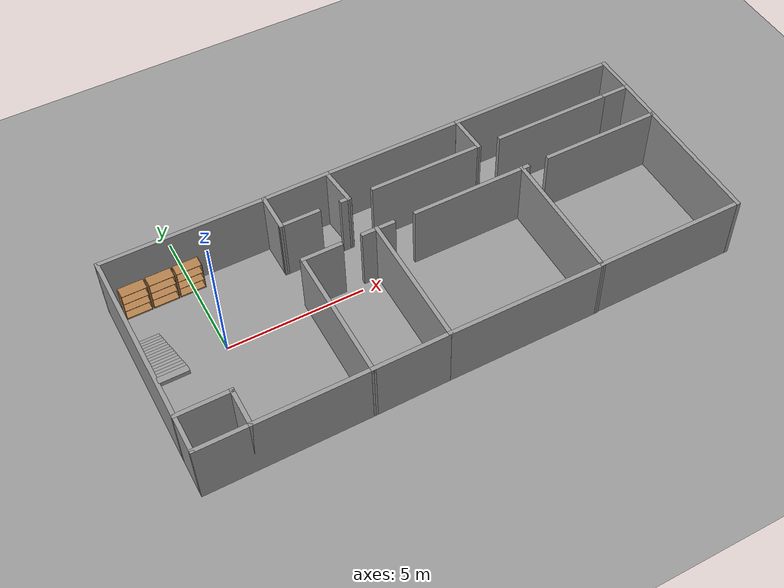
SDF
<sdf version="1.6">
 <world name="default">
  <light name="sun" type="directional">
   <pose>0 0 10 0 -0 0</pose>
   <diffuse>0.8 0.8 0.8 1</diffuse>
   <specular>0.2 0.2 0.2 1</specular>
   <attenuation>
    <range>1000</range>
    <constant>0.9</constant>
    <linear>0.01</linear>
    <quadratic>0.001</quadratic>
   </attenuation>
   <direction>0.5 0.1 -0.9</direction>
  </light>
  <scene><ambient>0.4 0.4 0.4 1</ambient><background>0.7 0.7 0.7 1</background><shadows>1</shadows></scene>
  <physics name="default_physics" default="0" type="ode">
   <max_step_size>0.01</max_step_size>
   <real_time_factor>1</real_time_factor>
   <real_time_update_rate>100</real_time_update_rate>
  </physics>
  <model name="ground_plane_0">
   <static>1</static>
   <link name="link">
    <collision name="collision">
     <geometry><plane><normal>0 0 1</normal><size>100 100</size></plane></geometry>
     <surface><friction><ode><mu>100</mu><mu2>50</mu2></ode></friction></surface>
    </collision>
    <visual name="visual">
     <cast_shadows>0</cast_shadows>
     <geometry><plane><normal>0 0 1</normal><size>100 100</size></plane></geometry>
     <material>
      <script><uri>file://media/materials/scripts/gazebo.material</uri><name>Gazebo/Grey</name></script>
     </material>
    </visual>
    <velocity_decay><linear>0</linear><angular>0</angular></velocity_decay>
   </link>
   <pose>0.497681 0 0 0 -0 0</pose>
  </model>
  <gravity>0 0 -9.8</gravity>
  <magnetic_field>6e-06 2.3e-05 -4.2e-05</magnetic_field>
  <atmosphere type="adiabatic"/>
  <spherical_coordinates>
   <surface_model>EARTH_WGS84</surface_model>
   <latitude_deg>0</latitude_deg>
   <longitude_deg>0</longitude_deg>
   <elevation>0</elevation>
   <heading_deg>0</heading_deg>
  </spherical_coordinates>
  <model name="inco_planta_baja_0">
   <link name="Stairs_0">
    <visual name="Stairs_0_Visual_2">
     <pose>-9.24623 1.59162 0.416667 0 -0 0</pose>
     <geometry><box><size>1 0.233333 0.166667</size></box></geometry>
     <material>
      <script><uri>file://media/materials/scripts/gazebo.material</uri><name>Gazebo/Grey</name></script>
      <ambient>1 1 1 1</ambient>
      <diffuse>0.7 0.7 0.7 1</diffuse>
      <specular>0.01 0.01 0.01 1</specular>
      <emissive>0 0 0 1</emissive>
     </material>
    </visual>
    <visual name="Stairs_0_Visual_0">
     <pose>-9.24623 2.05829 0.083333 0 -0 0</pose>
     <geometry><box><size>1 0.233333 0.166667</size></box></geometry>
     <material>
      <script><uri>file://media/materials/scripts/gazebo.material</uri><name>Gazebo/Grey</name></script>
      <ambient>1 1 1 1</ambient>
      <diffuse>0.7 0.7 0.7 1</diffuse>
      <specular>0.01 0.01 0.01 1</specular>
      <emissive>0 0 0 1</emissive>
     </material>
    </visual>
    <visual name="Stairs_0_Visual_1">
     <pose>-9.24623 1.82496 0.25 0 -0 0</pose>
     <geometry><box><size>1 0.233333 0.166667</size></box></geometry>
     <material>
      <script><uri>file://media/materials/scripts/gazebo.material</uri><name>Gazebo/Grey</name></script>
      <ambient>1 1 1 1</ambient>
      <diffuse>0.7 0.7 0.7 1</diffuse>
      <specular>0.01 0.01 0.01 1</specular>
      <emissive>0 0 0 1</emissive>
     </material>
    </visual>
    <visual name="Stairs_0_Visual_3">
     <pose>-9.24623 1.35829 0.583333 0 -0 0</pose>
     <geometry><box><size>1 0.233333 0.166667</size></box></geometry>
     <material>
      <script><uri>file://media/materials/scripts/gazebo.material</uri><name>Gazebo/Grey</name></script>
      <ambient>1 1 1 1</ambient>
      <diffuse>0.7 0.7 0.7 1</diffuse>
      <specular>0.01 0.01 0.01 1</specular>
      <emissive>0 0 0 1</emissive>
     </material>
    </visual>
    <visual name="Stairs_0_Visual_4">
     <pose>-9.24623 1.12495 0.75 0 -0 0</pose>
     <geometry><box><size>1 0.233333 0.166667</size></box></geometry>
     <material>
      <script><uri>file://media/materials/scripts/gazebo.material</uri><name>Gazebo/Grey</name></script>
      <ambient>1 1 1 1</ambient>
      <diffuse>0.7 0.7 0.7 1</diffuse>
      <specular>0.01 0.01 0.01 1</specular>
      <emissive>0 0 0 1</emissive>
     </material>
    </visual>
    <visual name="Stairs_0_Visual_5">
     <pose>-9.24623 0.891622 0.916667 0 -0 0</pose>
     <geometry><box><size>1 0.233333 0.166667</size></box></geometry>
     <material>
      <script><uri>file://media/materials/scripts/gazebo.material</uri><name>Gazebo/Grey</name></script>
      <ambient>1 1 1 1</ambient>
      <diffuse>0.7 0.7 0.7 1</diffuse>
      <specular>0.01 0.01 0.01 1</specular>
      <emissive>0 0 0 1</emissive>
     </material>
    </visual>
    <visual name="Stairs_0_Visual_6">
     <pose>-9.24623 0.658289 1.08333 0 -0 0</pose>
     <geometry><box><size>1 0.233333 0.166667</size></box></geometry>
     <material>
      <script><uri>file://media/materials/scripts/gazebo.material</uri><name>Gazebo/Grey</name></script>
      <ambient>1 1 1 1</ambient>
      <diffuse>0.7 0.7 0.7 1</diffuse>
      <specular>0.01 0.01 0.01 1</specular>
      <emissive>0 0 0 1</emissive>
     </material>
    </visual>
    <visual name="Stairs_0_Visual_8">
     <pose>-9.24623 0.191622 1.41667 0 -0 0</pose>
     <geometry><box><size>1 0.233333 0.166667</size></box></geometry>
     <material>
      <script><uri>file://media/materials/scripts/gazebo.material</uri><name>Gazebo/Grey</name></script>
      <ambient>1 1 1 1</ambient>
      <diffuse>0.7 0.7 0.7 1</diffuse>
      <specular>0.01 0.01 0.01 1</specular>
      <emissive>0 0 0 1</emissive>
     </material>
    </visual>
    <visual name="Stairs_0_Visual_7">
     <pose>-9.24623 0.424955 1.25 0 -0 0</pose>
     <geometry><box><size>1 0.233333 0.166667</size></box></geometry>
     <material>
      <script><uri>file://media/materials/scripts/gazebo.material</uri><name>Gazebo/Grey</name></script>
      <ambient>1 1 1 1</ambient>
      <diffuse>0.7 0.7 0.7 1</diffuse>
      <specular>0.01 0.01 0.01 1</specular>
      <emissive>0 0 0 1</emissive>
     </material>
    </visual>
    <visual name="Stairs_0_Visual_9">
     <pose>-9.24623 -0.041711 1.58333 0 -0 0</pose>
     <geometry><box><size>1 0.233333 0.166667</size></box></geometry>
     <material>
      <script><uri>file://media/materials/scripts/gazebo.material</uri><name>Gazebo/Grey</name></script>
      <ambient>1 1 1 1</ambient>
      <diffuse>0.7 0.7 0.7 1</diffuse>
      <specular>0.01 0.01 0.01 1</specular>
      <emissive>0 0 0 1</emissive>
     </material>
    </visual>
    <visual name="Stairs_0_Visual_10">
     <pose>-9.24623 -0.275045 1.75 0 -0 0</pose>
     <geometry><box><size>1 0.233333 0.166667</size></box></geometry>
     <material>
      <script><uri>file://media/materials/scripts/gazebo.material</uri><name>Gazebo/Grey</name></script>
      <ambient>1 1 1 1</ambient>
      <diffuse>0.7 0.7 0.7 1</diffuse>
      <specular>0.01 0.01 0.01 1</specular>
      <emissive>0 0 0 1</emissive>
     </material>
    </visual>
    <visual name="Stairs_0_Visual_11">
     <pose>-9.24623 -0.508378 1.91667 0 -0 0</pose>
     <geometry><box><size>1 0.233333 0.166667</size></box></geometry>
     <material>
      <script><uri>file://media/materials/scripts/gazebo.material</uri><name>Gazebo/Grey</name></script>
      <ambient>1 1 1 1</ambient>
      <diffuse>0.7 0.7 0.7 1</diffuse>
      <specular>0.01 0.01 0.01 1</specular>
      <emissive>0 0 0 1</emissive>
     </material>
    </visual>
    <visual name="Stairs_0_Visual_12">
     <pose>-9.24623 -0.741711 2.08333 0 -0 0</pose>
     <geometry><box><size>1 0.233333 0.166667</size></box></geometry>
     <material>
      <script><uri>file://media/materials/scripts/gazebo.material</uri><name>Gazebo/Grey</name></script>
      <ambient>1 1 1 1</ambient>
      <diffuse>0.7 0.7 0.7 1</diffuse>
      <specular>0.01 0.01 0.01 1</specular>
      <emissive>0 0 0 1</emissive>
     </material>
    </visual>
    <visual name="Stairs_0_Visual_13">
     <pose>-9.24623 -0.975045 2.25 0 -0 0</pose>
     <geometry><box><size>1 0.233333 0.166667</size></box></geometry>
     <material>
      <script><uri>file://media/materials/scripts/gazebo.material</uri><name>Gazebo/Grey</name></script>
      <ambient>1 1 1 1</ambient>
      <diffuse>0.7 0.7 0.7 1</diffuse>
      <specular>0.01 0.01 0.01 1</specular>
      <emissive>0 0 0 1</emissive>
     </material>
    </visual>
    <visual name="Stairs_0_Visual_14">
     <pose>-9.24623 -1.20838 2.41667 0 -0 0</pose>
     <geometry><box><size>1 0.233333 0.166667</size></box></geometry>
     <material>
      <script><uri>file://media/materials/scripts/gazebo.material</uri><name>Gazebo/Grey</name></script>
      <ambient>1 1 1 1</ambient>
      <diffuse>0.7 0.7 0.7 1</diffuse>
      <specular>0.01 0.01 0.01 1</specular>
      <emissive>0 0 0 1</emissive>
     </material>
    </visual>
    <collision name="Stairs_0_Collision_0">
     <pose>-9.24623 2.05829 0.083333 0 -0 0</pose>
     <geometry><box><size>1 0.233333 0.166667</size></box></geometry>
     <surface>
      <friction>
       <ode><mu>1</mu><mu2>1</mu2><fdir1>0 0 0</fdir1><slip1>0</slip1><slip2>0</slip2></ode>
       <torsional>
        <coefficient>1</coefficient>
        <patch_radius>0</patch_radius>
        <surface_radius>0</surface_radius>
        <use_patch_radius>1</use_patch_radius>
        <ode><slip>0</slip></ode>
       </torsional>
      </friction>
      <bounce><restitution_coefficient>0</restitution_coefficient><threshold>1e+06</threshold></bounce>
      <contact>
       <collide_without_contact>0</collide_without_contact>
       <collide_without_contact_bitmask>1</collide_without_contact_bitmask>
       <collide_bitmask>1</collide_bitmask>
       <ode>
        <soft_cfm>0</soft_cfm>
        <soft_erp>0.2</soft_erp>
        <kp>1e+13</kp>
        <kd>1</kd>
        <max_vel>0.01</max_vel>
        <min_depth>0</min_depth>
       </ode>
       <bullet>
        <split_impulse>1</split_impulse>
        <split_impulse_penetration_threshold>-0.01</split_impulse_penetration_threshold>
        <soft_cfm>0</soft_cfm>
        <soft_erp>0.2</soft_erp>
        <kp>1e+13</kp>
        <kd>1</kd>
       </bullet>
      </contact>
     </surface>
    </collision>
    <collision name="Stairs_0_Collision_1">
     <pose>-9.24623 1.82496 0.25 0 -0 0</pose>
     <geometry><box><size>1 0.233333 0.166667</size></box></geometry>
     <surface>
      <friction>
       <ode><mu>1</mu><mu2>1</mu2><fdir1>0 0 0</fdir1><slip1>0</slip1><slip2>0</slip2></ode>
       <torsional>
        <coefficient>1</coefficient>
        <patch_radius>0</patch_radius>
        <surface_radius>0</surface_radius>
        <use_patch_radius>1</use_patch_radius>
        <ode><slip>0</slip></ode>
       </torsional>
      </friction>
      <bounce><restitution_coefficient>0</restitution_coefficient><threshold>1e+06</threshold></bounce>
      <contact>
       <collide_without_contact>0</collide_without_contact>
       <collide_without_contact_bitmask>1</collide_without_contact_bitmask>
       <collide_bitmask>1</collide_bitmask>
       <ode>
        <soft_cfm>0</soft_cfm>
        <soft_erp>0.2</soft_erp>
        <kp>1e+13</kp>
        <kd>1</kd>
        <max_vel>0.01</max_vel>
        <min_depth>0</min_depth>
       </ode>
       <bullet>
        <split_impulse>1</split_impulse>
        <split_impulse_penetration_threshold>-0.01</split_impulse_penetration_threshold>
        <soft_cfm>0</soft_cfm>
        <soft_erp>0.2</soft_erp>
        <kp>1e+13</kp>
        <kd>1</kd>
       </bullet>
      </contact>
     </surface>
    </collision>
    <collision name="Stairs_0_Collision_7">
     <pose>-9.24623 0.424955 1.25 0 -0 0</pose>
     <geometry><box><size>1 0.233333 0.166667</size></box></geometry>
     <surface>
      <friction>
       <ode><mu>1</mu><mu2>1</mu2><fdir1>0 0 0</fdir1><slip1>0</slip1><slip2>0</slip2></ode>
       <torsional>
        <coefficient>1</coefficient>
        <patch_radius>0</patch_radius>
        <surface_radius>0</surface_radius>
        <use_patch_radius>1</use_patch_radius>
        <ode><slip>0</slip></ode>
       </torsional>
      </friction>
      <bounce><restitution_coefficient>0</restitution_coefficient><threshold>1e+06</threshold></bounce>
      <contact>
       <collide_without_contact>0</collide_without_contact>
       <collide_without_contact_bitmask>1</collide_without_contact_bitmask>
       <collide_bitmask>1</collide_bitmask>
       <ode>
        <soft_cfm>0</soft_cfm>
        <soft_erp>0.2</soft_erp>
        <kp>1e+13</kp>
        <kd>1</kd>
        <max_vel>0.01</max_vel>
        <min_depth>0</min_depth>
       </ode>
       <bullet>
        <split_impulse>1</split_impulse>
        <split_impulse_penetration_threshold>-0.01</split_impulse_penetration_threshold>
        <soft_cfm>0</soft_cfm>
        <soft_erp>0.2</soft_erp>
        <kp>1e+13</kp>
        <kd>1</kd>
       </bullet>
      </contact>
     </surface>
    </collision>
    <collision name="Stairs_0_Collision_2">
     <pose>-9.24623 1.59162 0.416667 0 -0 0</pose>
     <geometry><box><size>1 0.233333 0.166667</size></box></geometry>
     <surface>
      <friction>
       <ode><mu>1</mu><mu2>1</mu2><fdir1>0 0 0</fdir1><slip1>0</slip1><slip2>0</slip2></ode>
       <torsional>
        <coefficient>1</coefficient>
        <patch_radius>0</patch_radius>
        <surface_radius>0</surface_radius>
        <use_patch_radius>1</use_patch_radius>
        <ode><slip>0</slip></ode>
       </torsional>
      </friction>
      <bounce><restitution_coefficient>0</restitution_coefficient><threshold>1e+06</threshold></bounce>
      <contact>
       <collide_without_contact>0</collide_without_contact>
       <collide_without_contact_bitmask>1</collide_without_contact_bitmask>
       <collide_bitmask>1</collide_bitmask>
       <ode>
        <soft_cfm>0</soft_cfm>
        <soft_erp>0.2</soft_erp>
        <kp>1e+13</kp>
        <kd>1</kd>
        <max_vel>0.01</max_vel>
        <min_depth>0</min_depth>
       </ode>
       <bullet>
        <split_impulse>1</split_impulse>
        <split_impulse_penetration_threshold>-0.01</split_impulse_penetration_threshold>
        <soft_cfm>0</soft_cfm>
        <soft_erp>0.2</soft_erp>
        <kp>1e+13</kp>
        <kd>1</kd>
       </bullet>
      </contact>
     </surface>
    </collision>
    <collision name="Stairs_0_Collision_3">
     <pose>-9.24623 1.35829 0.583333 0 -0 0</pose>
     <geometry><box><size>1 0.233333 0.166667</size></box></geometry>
     <surface>
      <friction>
       <ode><mu>1</mu><mu2>1</mu2><fdir1>0 0 0</fdir1><slip1>0</slip1><slip2>0</slip2></ode>
       <torsional>
        <coefficient>1</coefficient>
        <patch_radius>0</patch_radius>
        <surface_radius>0</surface_radius>
        <use_patch_radius>1</use_patch_radius>
        <ode><slip>0</slip></ode>
       </torsional>
      </friction>
      <bounce><restitution_coefficient>0</restitution_coefficient><threshold>1e+06</threshold></bounce>
      <contact>
       <collide_without_contact>0</collide_without_contact>
       <collide_without_contact_bitmask>1</collide_without_contact_bitmask>
       <collide_bitmask>1</collide_bitmask>
       <ode>
        <soft_cfm>0</soft_cfm>
        <soft_erp>0.2</soft_erp>
        <kp>1e+13</kp>
        <kd>1</kd>
        <max_vel>0.01</max_vel>
        <min_depth>0</min_depth>
       </ode>
       <bullet>
        <split_impulse>1</split_impulse>
        <split_impulse_penetration_threshold>-0.01</split_impulse_penetration_threshold>
        <soft_cfm>0</soft_cfm>
        <soft_erp>0.2</soft_erp>
        <kp>1e+13</kp>
        <kd>1</kd>
       </bullet>
      </contact>
     </surface>
    </collision>
    <collision name="Stairs_0_Collision_4">
     <pose>-9.24623 1.12495 0.75 0 -0 0</pose>
     <geometry><box><size>1 0.233333 0.166667</size></box></geometry>
     <surface>
      <friction>
       <ode><mu>1</mu><mu2>1</mu2><fdir1>0 0 0</fdir1><slip1>0</slip1><slip2>0</slip2></ode>
       <torsional>
        <coefficient>1</coefficient>
        <patch_radius>0</patch_radius>
        <surface_radius>0</surface_radius>
        <use_patch_radius>1</use_patch_radius>
        <ode><slip>0</slip></ode>
       </torsional>
      </friction>
      <bounce><restitution_coefficient>0</restitution_coefficient><threshold>1e+06</threshold></bounce>
      <contact>
       <collide_without_contact>0</collide_without_contact>
       <collide_without_contact_bitmask>1</collide_without_contact_bitmask>
       <collide_bitmask>1</collide_bitmask>
       <ode>
        <soft_cfm>0</soft_cfm>
        <soft_erp>0.2</soft_erp>
        <kp>1e+13</kp>
        <kd>1</kd>
        <max_vel>0.01</max_vel>
        <min_depth>0</min_depth>
       </ode>
       <bullet>
        <split_impulse>1</split_impulse>
        <split_impulse_penetration_threshold>-0.01</split_impulse_penetration_threshold>
        <soft_cfm>0</soft_cfm>
        <soft_erp>0.2</soft_erp>
        <kp>1e+13</kp>
        <kd>1</kd>
       </bullet>
      </contact>
     </surface>
    </collision>
    <collision name="Stairs_0_Collision_5">
     <pose>-9.24623 0.891622 0.916667 0 -0 0</pose>
     <geometry><box><size>1 0.233333 0.166667</size></box></geometry>
     <surface>
      <friction>
       <ode><mu>1</mu><mu2>1</mu2><fdir1>0 0 0</fdir1><slip1>0</slip1><slip2>0</slip2></ode>
       <torsional>
        <coefficient>1</coefficient>
        <patch_radius>0</patch_radius>
        <surface_radius>0</surface_radius>
        <use_patch_radius>1</use_patch_radius>
        <ode><slip>0</slip></ode>
       </torsional>
      </friction>
      <bounce><restitution_coefficient>0</restitution_coefficient><threshold>1e+06</threshold></bounce>
      <contact>
       <collide_without_contact>0</collide_without_contact>
       <collide_without_contact_bitmask>1</collide_without_contact_bitmask>
       <collide_bitmask>1</collide_bitmask>
       <ode>
        <soft_cfm>0</soft_cfm>
        <soft_erp>0.2</soft_erp>
        <kp>1e+13</kp>
        <kd>1</kd>
        <max_vel>0.01</max_vel>
        <min_depth>0</min_depth>
       </ode>
       <bullet>
        <split_impulse>1</split_impulse>
        <split_impulse_penetration_threshold>-0.01</split_impulse_penetration_threshold>
        <soft_cfm>0</soft_cfm>
        <soft_erp>0.2</soft_erp>
        <kp>1e+13</kp>
        <kd>1</kd>
       </bullet>
      </contact>
     </surface>
    </collision>
    <collision name="Stairs_0_Collision_6">
     <pose>-9.24623 0.658289 1.08333 0 -0 0</pose>
     <geometry><box><size>1 0.233333 0.166667</size></box></geometry>
     <surface>
      <friction>
       <ode><mu>1</mu><mu2>1</mu2><fdir1>0 0 0</fdir1><slip1>0</slip1><slip2>0</slip2></ode>
       <torsional>
        <coefficient>1</coefficient>
        <patch_radius>0</patch_radius>
        <surface_radius>0</surface_radius>
        <use_patch_radius>1</use_patch_radius>
        <ode><slip>0</slip></ode>
       </torsional>
      </friction>
      <bounce><restitution_coefficient>0</restitution_coefficient><threshold>1e+06</threshold></bounce>
      <contact>
       <collide_without_contact>0</collide_without_contact>
       <collide_without_contact_bitmask>1</collide_without_contact_bitmask>
       <collide_bitmask>1</collide_bitmask>
       <ode>
        <soft_cfm>0</soft_cfm>
        <soft_erp>0.2</soft_erp>
        <kp>1e+13</kp>
        <kd>1</kd>
        <max_vel>0.01</max_vel>
        <min_depth>0</min_depth>
       </ode>
       <bullet>
        <split_impulse>1</split_impulse>
        <split_impulse_penetration_threshold>-0.01</split_impulse_penetration_threshold>
        <soft_cfm>0</soft_cfm>
        <soft_erp>0.2</soft_erp>
        <kp>1e+13</kp>
        <kd>1</kd>
       </bullet>
      </contact>
     </surface>
    </collision>
    <collision name="Stairs_0_Collision_8">
     <pose>-9.24623 0.191622 1.41667 0 -0 0</pose>
     <geometry><box><size>1 0.233333 0.166667</size></box></geometry>
     <surface>
      <friction>
       <ode><mu>1</mu><mu2>1</mu2><fdir1>0 0 0</fdir1><slip1>0</slip1><slip2>0</slip2></ode>
       <torsional>
        <coefficient>1</coefficient>
        <patch_radius>0</patch_radius>
        <surface_radius>0</surface_radius>
        <use_patch_radius>1</use_patch_radius>
        <ode><slip>0</slip></ode>
       </torsional>
      </friction>
      <bounce><restitution_coefficient>0</restitution_coefficient><threshold>1e+06</threshold></bounce>
      <contact>
       <collide_without_contact>0</collide_without_contact>
       <collide_without_contact_bitmask>1</collide_without_contact_bitmask>
       <collide_bitmask>1</collide_bitmask>
       <ode>
        <soft_cfm>0</soft_cfm>
        <soft_erp>0.2</soft_erp>
        <kp>1e+13</kp>
        <kd>1</kd>
        <max_vel>0.01</max_vel>
        <min_depth>0</min_depth>
       </ode>
       <bullet>
        <split_impulse>1</split_impulse>
        <split_impulse_penetration_threshold>-0.01</split_impulse_penetration_threshold>
        <soft_cfm>0</soft_cfm>
        <soft_erp>0.2</soft_erp>
        <kp>1e+13</kp>
        <kd>1</kd>
       </bullet>
      </contact>
     </surface>
    </collision>
    <collision name="Stairs_0_Collision_9">
     <pose>-9.24623 -0.041711 1.58333 0 -0 0</pose>
     <geometry><box><size>1 0.233333 0.166667</size></box></geometry>
     <surface>
      <friction>
       <ode><mu>1</mu><mu2>1</mu2><fdir1>0 0 0</fdir1><slip1>0</slip1><slip2>0</slip2></ode>
       <torsional>
        <coefficient>1</coefficient>
        <patch_radius>0</patch_radius>
        <surface_radius>0</surface_radius>
        <use_patch_radius>1</use_patch_radius>
        <ode><slip>0</slip></ode>
       </torsional>
      </friction>
      <bounce><restitution_coefficient>0</restitution_coefficient><threshold>1e+06</threshold></bounce>
      <contact>
       <collide_without_contact>0</collide_without_contact>
       <collide_without_contact_bitmask>1</collide_without_contact_bitmask>
       <collide_bitmask>1</collide_bitmask>
       <ode>
        <soft_cfm>0</soft_cfm>
        <soft_erp>0.2</soft_erp>
        <kp>1e+13</kp>
        <kd>1</kd>
        <max_vel>0.01</max_vel>
        <min_depth>0</min_depth>
       </ode>
       <bullet>
        <split_impulse>1</split_impulse>
        <split_impulse_penetration_threshold>-0.01</split_impulse_penetration_threshold>
        <soft_cfm>0</soft_cfm>
        <soft_erp>0.2</soft_erp>
        <kp>1e+13</kp>
        <kd>1</kd>
       </bullet>
      </contact>
     </surface>
    </collision>
    <collision name="Stairs_0_Collision_10">
     <pose>-9.24623 -0.275045 1.75 0 -0 0</pose>
     <geometry><box><size>1 0.233333 0.166667</size></box></geometry>
     <surface>
      <friction>
       <ode><mu>1</mu><mu2>1</mu2><fdir1>0 0 0</fdir1><slip1>0</slip1><slip2>0</slip2></ode>
       <torsional>
        <coefficient>1</coefficient>
        <patch_radius>0</patch_radius>
        <surface_radius>0</surface_radius>
        <use_patch_radius>1</use_patch_radius>
        <ode><slip>0</slip></ode>
       </torsional>
      </friction>
      <bounce><restitution_coefficient>0</restitution_coefficient><threshold>1e+06</threshold></bounce>
      <contact>
       <collide_without_contact>0</collide_without_contact>
       <collide_without_contact_bitmask>1</collide_without_contact_bitmask>
       <collide_bitmask>1</collide_bitmask>
       <ode>
        <soft_cfm>0</soft_cfm>
        <soft_erp>0.2</soft_erp>
        <kp>1e+13</kp>
        <kd>1</kd>
        <max_vel>0.01</max_vel>
        <min_depth>0</min_depth>
       </ode>
       <bullet>
        <split_impulse>1</split_impulse>
        <split_impulse_penetration_threshold>-0.01</split_impulse_penetration_threshold>
        <soft_cfm>0</soft_cfm>
        <soft_erp>0.2</soft_erp>
        <kp>1e+13</kp>
        <kd>1</kd>
       </bullet>
      </contact>
     </surface>
    </collision>
    <collision name="Stairs_0_Collision_11">
     <pose>-9.24623 -0.508378 1.91667 0 -0 0</pose>
     <geometry><box><size>1 0.233333 0.166667</size></box></geometry>
     <surface>
      <friction>
       <ode><mu>1</mu><mu2>1</mu2><fdir1>0 0 0</fdir1><slip1>0</slip1><slip2>0</slip2></ode>
       <torsional>
        <coefficient>1</coefficient>
        <patch_radius>0</patch_radius>
        <surface_radius>0</surface_radius>
        <use_patch_radius>1</use_patch_radius>
        <ode><slip>0</slip></ode>
       </torsional>
      </friction>
      <bounce><restitution_coefficient>0</restitution_coefficient><threshold>1e+06</threshold></bounce>
      <contact>
       <collide_without_contact>0</collide_without_contact>
       <collide_without_contact_bitmask>1</collide_without_contact_bitmask>
       <collide_bitmask>1</collide_bitmask>
       <ode>
        <soft_cfm>0</soft_cfm>
        <soft_erp>0.2</soft_erp>
        <kp>1e+13</kp>
        <kd>1</kd>
        <max_vel>0.01</max_vel>
        <min_depth>0</min_depth>
       </ode>
       <bullet>
        <split_impulse>1</split_impulse>
        <split_impulse_penetration_threshold>-0.01</split_impulse_penetration_threshold>
        <soft_cfm>0</soft_cfm>
        <soft_erp>0.2</soft_erp>
        <kp>1e+13</kp>
        <kd>1</kd>
       </bullet>
      </contact>
     </surface>
    </collision>
    <collision name="Stairs_0_Collision_13">
     <pose>-9.24623 -0.975045 2.25 0 -0 0</pose>
     <geometry><box><size>1 0.233333 0.166667</size></box></geometry>
     <surface>
      <friction>
       <ode><mu>1</mu><mu2>1</mu2><fdir1>0 0 0</fdir1><slip1>0</slip1><slip2>0</slip2></ode>
       <torsional>
        <coefficient>1</coefficient>
        <patch_radius>0</patch_radius>
        <surface_radius>0</surface_radius>
        <use_patch_radius>1</use_patch_radius>
        <ode><slip>0</slip></ode>
       </torsional>
      </friction>
      <bounce><restitution_coefficient>0</restitution_coefficient><threshold>1e+06</threshold></bounce>
      <contact>
       <collide_without_contact>0</collide_without_contact>
       <collide_without_contact_bitmask>1</collide_without_contact_bitmask>
       <collide_bitmask>1</collide_bitmask>
       <ode>
        <soft_cfm>0</soft_cfm>
        <soft_erp>0.2</soft_erp>
        <kp>1e+13</kp>
        <kd>1</kd>
        <max_vel>0.01</max_vel>
        <min_depth>0</min_depth>
       </ode>
       <bullet>
        <split_impulse>1</split_impulse>
        <split_impulse_penetration_threshold>-0.01</split_impulse_penetration_threshold>
        <soft_cfm>0</soft_cfm>
        <soft_erp>0.2</soft_erp>
        <kp>1e+13</kp>
        <kd>1</kd>
       </bullet>
      </contact>
     </surface>
    </collision>
    <collision name="Stairs_0_Collision_12">
     <pose>-9.24623 -0.741711 2.08333 0 -0 0</pose>
     <geometry><box><size>1 0.233333 0.166667</size></box></geometry>
     <surface>
      <friction>
       <ode><mu>1</mu><mu2>1</mu2><fdir1>0 0 0</fdir1><slip1>0</slip1><slip2>0</slip2></ode>
       <torsional>
        <coefficient>1</coefficient>
        <patch_radius>0</patch_radius>
        <surface_radius>0</surface_radius>
        <use_patch_radius>1</use_patch_radius>
        <ode><slip>0</slip></ode>
       </torsional>
      </friction>
      <bounce><restitution_coefficient>0</restitution_coefficient><threshold>1e+06</threshold></bounce>
      <contact>
       <collide_without_contact>0</collide_without_contact>
       <collide_without_contact_bitmask>1</collide_without_contact_bitmask>
       <collide_bitmask>1</collide_bitmask>
       <ode>
        <soft_cfm>0</soft_cfm>
        <soft_erp>0.2</soft_erp>
        <kp>1e+13</kp>
        <kd>1</kd>
        <max_vel>0.01</max_vel>
        <min_depth>0</min_depth>
       </ode>
       <bullet>
        <split_impulse>1</split_impulse>
        <split_impulse_penetration_threshold>-0.01</split_impulse_penetration_threshold>
        <soft_cfm>0</soft_cfm>
        <soft_erp>0.2</soft_erp>
        <kp>1e+13</kp>
        <kd>1</kd>
       </bullet>
      </contact>
     </surface>
    </collision>
    <collision name="Stairs_0_Collision_14">
     <pose>-9.24623 -1.20838 2.41667 0 -0 0</pose>
     <geometry><box><size>1 0.233333 0.166667</size></box></geometry>
     <surface>
      <friction>
       <ode><mu>1</mu><mu2>1</mu2><fdir1>0 0 0</fdir1><slip1>0</slip1><slip2>0</slip2></ode>
       <torsional>
        <coefficient>1</coefficient>
        <patch_radius>0</patch_radius>
        <surface_radius>0</surface_radius>
        <use_patch_radius>1</use_patch_radius>
        <ode><slip>0</slip></ode>
       </torsional>
      </friction>
      <bounce><restitution_coefficient>0</restitution_coefficient><threshold>1e+06</threshold></bounce>
      <contact>
       <collide_without_contact>0</collide_without_contact>
       <collide_without_contact_bitmask>1</collide_without_contact_bitmask>
       <collide_bitmask>1</collide_bitmask>
       <ode>
        <soft_cfm>0</soft_cfm>
        <soft_erp>0.2</soft_erp>
        <kp>1e+13</kp>
        <kd>1</kd>
        <max_vel>0.01</max_vel>
        <min_depth>0</min_depth>
       </ode>
       <bullet>
        <split_impulse>1</split_impulse>
        <split_impulse_penetration_threshold>-0.01</split_impulse_penetration_threshold>
        <soft_cfm>0</soft_cfm>
        <soft_erp>0.2</soft_erp>
        <kp>1e+13</kp>
        <kd>1</kd>
       </bullet>
      </contact>
     </surface>
    </collision>
   </link>
   <link name="Wall_10">
    <pose>-3.93462 3.232 0 0 0 -1.5727</pose>
    <visual name="Wall_10_Visual">
     <pose>0 0 1.25 0 -0 0</pose>
     <geometry><box><size>1.48163 0.15 2.5</size></box></geometry>
     <material>
      <script><uri>file://media/materials/scripts/gazebo.material</uri><name>Gazebo/Grey</name></script>
      <ambient>1 1 1 1</ambient>
      <diffuse>0.7 0.7 0.7 1</diffuse>
      <specular>0.01 0.01 0.01 1</specular>
      <emissive>0 0 0 1</emissive>
     </material>
    </visual>
    <collision name="Wall_10_Collision">
     <pose>0 0 1.25 0 -0 0</pose>
     <geometry><box><size>1.48163 0.15 2.5</size></box></geometry>
     <surface>
      <friction>
       <ode><mu>1</mu><mu2>1</mu2><fdir1>0 0 0</fdir1><slip1>0</slip1><slip2>0</slip2></ode>
       <torsional>
        <coefficient>1</coefficient>
        <patch_radius>0</patch_radius>
        <surface_radius>0</surface_radius>
        <use_patch_radius>1</use_patch_radius>
        <ode><slip>0</slip></ode>
       </torsional>
      </friction>
      <bounce><restitution_coefficient>0</restitution_coefficient><threshold>1e+06</threshold></bounce>
      <contact>
       <collide_without_contact>0</collide_without_contact>
       <collide_without_contact_bitmask>1</collide_without_contact_bitmask>
       <collide_bitmask>1</collide_bitmask>
       <ode>
        <soft_cfm>0</soft_cfm>
        <soft_erp>0.2</soft_erp>
        <kp>1e+13</kp>
        <kd>1</kd>
        <max_vel>0.01</max_vel>
        <min_depth>0</min_depth>
       </ode>
       <bullet>
        <split_impulse>1</split_impulse>
        <split_impulse_penetration_threshold>-0.01</split_impulse_penetration_threshold>
        <soft_cfm>0</soft_cfm>
        <soft_erp>0.2</soft_erp>
        <kp>1e+13</kp>
        <kd>1</kd>
       </bullet>
      </contact>
     </surface>
    </collision>
   </link>
   <link name="Wall_12">
    <pose>-3.26089 2.56618 0 0 -0 0</pose>
    <visual name="Wall_12_Visual">
     <pose>0 0 1.25 0 -0 0</pose>
     <geometry><box><size>1.5 0.15 2.5</size></box></geometry>
     <material>
      <script><uri>file://media/materials/scripts/gazebo.material</uri><name>Gazebo/Grey</name></script>
      <ambient>1 1 1 1</ambient>
      <diffuse>0.7 0.7 0.7 1</diffuse>
      <specular>0.01 0.01 0.01 1</specular>
      <emissive>0 0 0 1</emissive>
     </material>
    </visual>
    <collision name="Wall_12_Collision">
     <pose>0 0 1.25 0 -0 0</pose>
     <geometry><box><size>1.5 0.15 2.5</size></box></geometry>
     <surface>
      <friction>
       <ode><mu>1</mu><mu2>1</mu2><fdir1>0 0 0</fdir1><slip1>0</slip1><slip2>0</slip2></ode>
       <torsional>
        <coefficient>1</coefficient>
        <patch_radius>0</patch_radius>
        <surface_radius>0</surface_radius>
        <use_patch_radius>1</use_patch_radius>
        <ode><slip>0</slip></ode>
       </torsional>
      </friction>
      <bounce><restitution_coefficient>0</restitution_coefficient><threshold>1e+06</threshold></bounce>
      <contact>
       <collide_without_contact>0</collide_without_contact>
       <collide_without_contact_bitmask>1</collide_without_contact_bitmask>
       <collide_bitmask>1</collide_bitmask>
       <ode>
        <soft_cfm>0</soft_cfm>
        <soft_erp>0.2</soft_erp>
        <kp>1e+13</kp>
        <kd>1</kd>
        <max_vel>0.01</max_vel>
        <min_depth>0</min_depth>
       </ode>
       <bullet>
        <split_impulse>1</split_impulse>
        <split_impulse_penetration_threshold>-0.01</split_impulse_penetration_threshold>
        <soft_cfm>0</soft_cfm>
        <soft_erp>0.2</soft_erp>
        <kp>1e+13</kp>
        <kd>1</kd>
       </bullet>
      </contact>
     </surface>
    </collision>
   </link>
   <link name="Wall_126">
    <pose>9.78501 1.72965 0 0 -0 1.5708</pose>
    <visual name="Wall_126_Visual">
     <pose>0 0 1.25 0 -0 0</pose>
     <geometry><box><size>1.75 0.15 2.5</size></box></geometry>
     <material>
      <script><uri>file://media/materials/scripts/gazebo.material</uri><name>Gazebo/Grey</name></script>
      <ambient>1 1 1 1</ambient>
      <diffuse>0.7 0.7 0.7 1</diffuse>
      <specular>0.01 0.01 0.01 1</specular>
      <emissive>0 0 0 1</emissive>
     </material>
    </visual>
    <collision name="Wall_126_Collision">
     <pose>0 0 1.25 0 -0 0</pose>
     <geometry><box><size>1.75 0.15 2.5</size></box></geometry>
     <surface>
      <friction>
       <ode><mu>1</mu><mu2>1</mu2><fdir1>0 0 0</fdir1><slip1>0</slip1><slip2>0</slip2></ode>
       <torsional>
        <coefficient>1</coefficient>
        <patch_radius>0</patch_radius>
        <surface_radius>0</surface_radius>
        <use_patch_radius>1</use_patch_radius>
        <ode><slip>0</slip></ode>
       </torsional>
      </friction>
      <bounce><restitution_coefficient>0</restitution_coefficient><threshold>1e+06</threshold></bounce>
      <contact>
       <collide_without_contact>0</collide_without_contact>
       <collide_without_contact_bitmask>1</collide_without_contact_bitmask>
       <collide_bitmask>1</collide_bitmask>
       <ode>
        <soft_cfm>0</soft_cfm>
        <soft_erp>0.2</soft_erp>
        <kp>1e+13</kp>
        <kd>1</kd>
        <max_vel>0.01</max_vel>
        <min_depth>0</min_depth>
       </ode>
       <bullet>
        <split_impulse>1</split_impulse>
        <split_impulse_penetration_threshold>-0.01</split_impulse_penetration_threshold>
        <soft_cfm>0</soft_cfm>
        <soft_erp>0.2</soft_erp>
        <kp>1e+13</kp>
        <kd>1</kd>
       </bullet>
      </contact>
     </surface>
    </collision>
   </link>
   <link name="Wall_127">
    <pose>9.29747 2.53004 0 0 -0 3.1408</pose>
    <visual name="Wall_127_Visual">
     <pose>0 0 1.25 0 -0 0</pose>
     <geometry><box><size>1.12508 0.15 2.5</size></box></geometry>
     <material>
      <script><uri>file://media/materials/scripts/gazebo.material</uri><name>Gazebo/Grey</name></script>
      <ambient>1 1 1 1</ambient>
      <diffuse>0.7 0.7 0.7 1</diffuse>
      <specular>0.01 0.01 0.01 1</specular>
      <emissive>0 0 0 1</emissive>
     </material>
    </visual>
    <collision name="Wall_127_Collision">
     <pose>0 0 1.25 0 -0 0</pose>
     <geometry><box><size>1.12508 0.15 2.5</size></box></geometry>
     <surface>
      <friction>
       <ode><mu>1</mu><mu2>1</mu2><fdir1>0 0 0</fdir1><slip1>0</slip1><slip2>0</slip2></ode>
       <torsional>
        <coefficient>1</coefficient>
        <patch_radius>0</patch_radius>
        <surface_radius>0</surface_radius>
        <use_patch_radius>1</use_patch_radius>
        <ode><slip>0</slip></ode>
       </torsional>
      </friction>
      <bounce><restitution_coefficient>0</restitution_coefficient><threshold>1e+06</threshold></bounce>
      <contact>
       <collide_without_contact>0</collide_without_contact>
       <collide_without_contact_bitmask>1</collide_without_contact_bitmask>
       <collide_bitmask>1</collide_bitmask>
       <ode>
        <soft_cfm>0</soft_cfm>
        <soft_erp>0.2</soft_erp>
        <kp>1e+13</kp>
        <kd>1</kd>
        <max_vel>0.01</max_vel>
        <min_depth>0</min_depth>
       </ode>
       <bullet>
        <split_impulse>1</split_impulse>
        <split_impulse_penetration_threshold>-0.01</split_impulse_penetration_threshold>
        <soft_cfm>0</soft_cfm>
        <soft_erp>0.2</soft_erp>
        <kp>1e+13</kp>
        <kd>1</kd>
       </bullet>
      </contact>
     </surface>
    </collision>
   </link>
   <link name="Wall_129">
    <pose>-1.23779 -1.49163 0 0 0 -1.5708</pose>
    <visual name="Wall_129_Visual">
     <pose>0 0 1.25 0 -0 0</pose>
     <geometry><box><size>5 0.15 2.5</size></box></geometry>
     <material>
      <script><uri>file://media/materials/scripts/gazebo.material</uri><name>Gazebo/Grey</name></script>
      <ambient>1 1 1 1</ambient>
      <diffuse>0.7 0.7 0.7 1</diffuse>
      <specular>0.01 0.01 0.01 1</specular>
      <emissive>0 0 0 1</emissive>
     </material>
    </visual>
    <collision name="Wall_129_Collision">
     <pose>0 0 1.25 0 -0 0</pose>
     <geometry><box><size>5 0.15 2.5</size></box></geometry>
     <surface>
      <friction>
       <ode><mu>1</mu><mu2>1</mu2><fdir1>0 0 0</fdir1><slip1>0</slip1><slip2>0</slip2></ode>
       <torsional>
        <coefficient>1</coefficient>
        <patch_radius>0</patch_radius>
        <surface_radius>0</surface_radius>
        <use_patch_radius>1</use_patch_radius>
        <ode><slip>0</slip></ode>
       </torsional>
      </friction>
      <bounce><restitution_coefficient>0</restitution_coefficient><threshold>1e+06</threshold></bounce>
      <contact>
       <collide_without_contact>0</collide_without_contact>
       <collide_without_contact_bitmask>1</collide_without_contact_bitmask>
       <collide_bitmask>1</collide_bitmask>
       <ode>
        <soft_cfm>0</soft_cfm>
        <soft_erp>0.2</soft_erp>
        <kp>1e+13</kp>
        <kd>1</kd>
        <max_vel>0.01</max_vel>
        <min_depth>0</min_depth>
       </ode>
       <bullet>
        <split_impulse>1</split_impulse>
        <split_impulse_penetration_threshold>-0.01</split_impulse_penetration_threshold>
        <soft_cfm>0</soft_cfm>
        <soft_erp>0.2</soft_erp>
        <kp>1e+13</kp>
        <kd>1</kd>
       </bullet>
      </contact>
     </surface>
    </collision>
   </link>
   <link name="Wall_130">
    <pose>-2.58684 -3.92522 0 0 0 -3.13522</pose>
    <visual name="Wall_130_Visual">
     <pose>0 0 1.25 0 -0 0</pose>
     <geometry><box><size>2.84815 0.15 2.5</size></box></geometry>
     <material>
      <script><uri>file://media/materials/scripts/gazebo.material</uri><name>Gazebo/Grey</name></script>
      <ambient>1 1 1 1</ambient>
      <diffuse>0.7 0.7 0.7 1</diffuse>
      <specular>0.01 0.01 0.01 1</specular>
      <emissive>0 0 0 1</emissive>
     </material>
    </visual>
    <collision name="Wall_130_Collision">
     <pose>0 0 1.25 0 -0 0</pose>
     <geometry><box><size>2.84815 0.15 2.5</size></box></geometry>
     <surface>
      <friction>
       <ode><mu>1</mu><mu2>1</mu2><fdir1>0 0 0</fdir1><slip1>0</slip1><slip2>0</slip2></ode>
       <torsional>
        <coefficient>1</coefficient>
        <patch_radius>0</patch_radius>
        <surface_radius>0</surface_radius>
        <use_patch_radius>1</use_patch_radius>
        <ode><slip>0</slip></ode>
       </torsional>
      </friction>
      <bounce><restitution_coefficient>0</restitution_coefficient><threshold>1e+06</threshold></bounce>
      <contact>
       <collide_without_contact>0</collide_without_contact>
       <collide_without_contact_bitmask>1</collide_without_contact_bitmask>
       <collide_bitmask>1</collide_bitmask>
       <ode>
        <soft_cfm>0</soft_cfm>
        <soft_erp>0.2</soft_erp>
        <kp>1e+13</kp>
        <kd>1</kd>
        <max_vel>0.01</max_vel>
        <min_depth>0</min_depth>
       </ode>
       <bullet>
        <split_impulse>1</split_impulse>
        <split_impulse_penetration_threshold>-0.01</split_impulse_penetration_threshold>
        <soft_cfm>0</soft_cfm>
        <soft_erp>0.2</soft_erp>
        <kp>1e+13</kp>
        <kd>1</kd>
       </bullet>
      </contact>
     </surface>
    </collision>
   </link>
   <link name="Wall_132">
    <pose>1.56221 -3.9268 0 0 0 -0.003633</pose>
    <visual name="Wall_132_Visual">
     <pose>0 0 1.25 0 -0 0</pose>
     <geometry><box><size>5.75 0.15 2.5</size></box></geometry>
     <material>
      <script><uri>file://media/materials/scripts/gazebo.material</uri><name>Gazebo/Grey</name></script>
      <ambient>1 1 1 1</ambient>
      <diffuse>0.7 0.7 0.7 1</diffuse>
      <specular>0.01 0.01 0.01 1</specular>
      <emissive>0 0 0 1</emissive>
     </material>
    </visual>
    <collision name="Wall_132_Collision">
     <pose>0 0 1.25 0 -0 0</pose>
     <geometry><box><size>5.75 0.15 2.5</size></box></geometry>
     <surface>
      <friction>
       <ode><mu>1</mu><mu2>1</mu2><fdir1>0 0 0</fdir1><slip1>0</slip1><slip2>0</slip2></ode>
       <torsional>
        <coefficient>1</coefficient>
        <patch_radius>0</patch_radius>
        <surface_radius>0</surface_radius>
        <use_patch_radius>1</use_patch_radius>
        <ode><slip>0</slip></ode>
       </torsional>
      </friction>
      <bounce><restitution_coefficient>0</restitution_coefficient><threshold>1e+06</threshold></bounce>
      <contact>
       <collide_without_contact>0</collide_without_contact>
       <collide_without_contact_bitmask>1</collide_without_contact_bitmask>
       <collide_bitmask>1</collide_bitmask>
       <ode>
        <soft_cfm>0</soft_cfm>
        <soft_erp>0.2</soft_erp>
        <kp>1e+13</kp>
        <kd>1</kd>
        <max_vel>0.01</max_vel>
        <min_depth>0</min_depth>
       </ode>
       <bullet>
        <split_impulse>1</split_impulse>
        <split_impulse_penetration_threshold>-0.01</split_impulse_penetration_threshold>
        <soft_cfm>0</soft_cfm>
        <soft_erp>0.2</soft_erp>
        <kp>1e+13</kp>
        <kd>1</kd>
       </bullet>
      </contact>
     </surface>
    </collision>
   </link>
   <link name="Wall_133">
    <pose>4.36221 -1.5018 0 0 -0 1.5708</pose>
    <visual name="Wall_133_Visual">
     <pose>0 0 1.25 0 -0 0</pose>
     <geometry><box><size>5.02034 0.15 2.5</size></box></geometry>
     <material>
      <script><uri>file://media/materials/scripts/gazebo.material</uri><name>Gazebo/Grey</name></script>
      <ambient>1 1 1 1</ambient>
      <diffuse>0.7 0.7 0.7 1</diffuse>
      <specular>0.01 0.01 0.01 1</specular>
      <emissive>0 0 0 1</emissive>
     </material>
    </visual>
    <collision name="Wall_133_Collision">
     <pose>0 0 1.25 0 -0 0</pose>
     <geometry><box><size>5.02034 0.15 2.5</size></box></geometry>
     <surface>
      <friction>
       <ode><mu>1</mu><mu2>1</mu2><fdir1>0 0 0</fdir1><slip1>0</slip1><slip2>0</slip2></ode>
       <torsional>
        <coefficient>1</coefficient>
        <patch_radius>0</patch_radius>
        <surface_radius>0</surface_radius>
        <use_patch_radius>1</use_patch_radius>
        <ode><slip>0</slip></ode>
       </torsional>
      </friction>
      <bounce><restitution_coefficient>0</restitution_coefficient><threshold>1e+06</threshold></bounce>
      <contact>
       <collide_without_contact>0</collide_without_contact>
       <collide_without_contact_bitmask>1</collide_without_contact_bitmask>
       <collide_bitmask>1</collide_bitmask>
       <ode>
        <soft_cfm>0</soft_cfm>
        <soft_erp>0.2</soft_erp>
        <kp>1e+13</kp>
        <kd>1</kd>
        <max_vel>0.01</max_vel>
        <min_depth>0</min_depth>
       </ode>
       <bullet>
        <split_impulse>1</split_impulse>
        <split_impulse_penetration_threshold>-0.01</split_impulse_penetration_threshold>
        <soft_cfm>0</soft_cfm>
        <soft_erp>0.2</soft_erp>
        <kp>1e+13</kp>
        <kd>1</kd>
       </bullet>
      </contact>
     </surface>
    </collision>
   </link>
   <link name="Wall_135">
    <pose>7.03721 -3.91663 0 0 -0 0</pose>
    <visual name="Wall_135_Visual">
     <pose>0 0 1.25 0 -0 0</pose>
     <geometry><box><size>5.5 0.15 2.5</size></box></geometry>
     <material>
      <script><uri>file://media/materials/scripts/gazebo.material</uri><name>Gazebo/Grey</name></script>
      <ambient>1 1 1 1</ambient>
      <diffuse>0.7 0.7 0.7 1</diffuse>
      <specular>0.01 0.01 0.01 1</specular>
      <emissive>0 0 0 1</emissive>
     </material>
    </visual>
    <collision name="Wall_135_Collision">
     <pose>0 0 1.25 0 -0 0</pose>
     <geometry><box><size>5.5 0.15 2.5</size></box></geometry>
     <surface>
      <friction>
       <ode><mu>1</mu><mu2>1</mu2><fdir1>0 0 0</fdir1><slip1>0</slip1><slip2>0</slip2></ode>
       <torsional>
        <coefficient>1</coefficient>
        <patch_radius>0</patch_radius>
        <surface_radius>0</surface_radius>
        <use_patch_radius>1</use_patch_radius>
        <ode><slip>0</slip></ode>
       </torsional>
      </friction>
      <bounce><restitution_coefficient>0</restitution_coefficient><threshold>1e+06</threshold></bounce>
      <contact>
       <collide_without_contact>0</collide_without_contact>
       <collide_without_contact_bitmask>1</collide_without_contact_bitmask>
       <collide_bitmask>1</collide_bitmask>
       <ode>
        <soft_cfm>0</soft_cfm>
        <soft_erp>0.2</soft_erp>
        <kp>1e+13</kp>
        <kd>1</kd>
        <max_vel>0.01</max_vel>
        <min_depth>0</min_depth>
       </ode>
       <bullet>
        <split_impulse>1</split_impulse>
        <split_impulse_penetration_threshold>-0.01</split_impulse_penetration_threshold>
        <soft_cfm>0</soft_cfm>
        <soft_erp>0.2</soft_erp>
        <kp>1e+13</kp>
        <kd>1</kd>
       </bullet>
      </contact>
     </surface>
    </collision>
   </link>
   <link name="Wall_137">
    <pose>9.78501 -1.49535 0 0 0 -1.5708</pose>
    <visual name="Wall_137_Visual">
     <pose>0 0 1.25 0 -0 0</pose>
     <geometry><box><size>5 0.15 2.5</size></box></geometry>
     <material>
      <script><uri>file://media/materials/scripts/gazebo.material</uri><name>Gazebo/Grey</name></script>
      <ambient>1 1 1 1</ambient>
      <diffuse>0.7 0.7 0.7 1</diffuse>
      <specular>0.01 0.01 0.01 1</specular>
      <emissive>0 0 0 1</emissive>
     </material>
    </visual>
    <collision name="Wall_137_Collision">
     <pose>0 0 1.25 0 -0 0</pose>
     <geometry><box><size>5 0.15 2.5</size></box></geometry>
     <surface>
      <friction>
       <ode><mu>1</mu><mu2>1</mu2><fdir1>0 0 0</fdir1><slip1>0</slip1><slip2>0</slip2></ode>
       <torsional>
        <coefficient>1</coefficient>
        <patch_radius>0</patch_radius>
        <surface_radius>0</surface_radius>
        <use_patch_radius>1</use_patch_radius>
        <ode><slip>0</slip></ode>
       </torsional>
      </friction>
      <bounce><restitution_coefficient>0</restitution_coefficient><threshold>1e+06</threshold></bounce>
      <contact>
       <collide_without_contact>0</collide_without_contact>
       <collide_without_contact_bitmask>1</collide_without_contact_bitmask>
       <collide_bitmask>1</collide_bitmask>
       <ode>
        <soft_cfm>0</soft_cfm>
        <soft_erp>0.2</soft_erp>
        <kp>1e+13</kp>
        <kd>1</kd>
        <max_vel>0.01</max_vel>
        <min_depth>0</min_depth>
       </ode>
       <bullet>
        <split_impulse>1</split_impulse>
        <split_impulse_penetration_threshold>-0.01</split_impulse_penetration_threshold>
        <soft_cfm>0</soft_cfm>
        <soft_erp>0.2</soft_erp>
        <kp>1e+13</kp>
        <kd>1</kd>
       </bullet>
      </contact>
     </surface>
    </collision>
   </link>
   <link name="Wall_139">
    <pose>-2.75835 3.91357 0 0 -0 0.008489</pose>
    <visual name="Wall_139_Visual">
     <pose>0 0 1.25 0 -0 0</pose>
     <geometry><box><size>2.50008 0.15 2.5</size></box></geometry>
     <material>
      <script><uri>file://media/materials/scripts/gazebo.material</uri><name>Gazebo/Grey</name></script>
      <ambient>1 1 1 1</ambient>
      <diffuse>0.7 0.7 0.7 1</diffuse>
      <specular>0.01 0.01 0.01 1</specular>
      <emissive>0 0 0 1</emissive>
     </material>
    </visual>
    <collision name="Wall_139_Collision">
     <pose>0 0 1.25 0 -0 0</pose>
     <geometry><box><size>2.50008 0.15 2.5</size></box></geometry>
     <surface>
      <friction>
       <ode><mu>1</mu><mu2>1</mu2><fdir1>0 0 0</fdir1><slip1>0</slip1><slip2>0</slip2></ode>
       <torsional>
        <coefficient>1</coefficient>
        <patch_radius>0</patch_radius>
        <surface_radius>0</surface_radius>
        <use_patch_radius>1</use_patch_radius>
        <ode><slip>0</slip></ode>
       </torsional>
      </friction>
      <bounce><restitution_coefficient>0</restitution_coefficient><threshold>1e+06</threshold></bounce>
      <contact>
       <collide_without_contact>0</collide_without_contact>
       <collide_without_contact_bitmask>1</collide_without_contact_bitmask>
       <collide_bitmask>1</collide_bitmask>
       <ode>
        <soft_cfm>0</soft_cfm>
        <soft_erp>0.2</soft_erp>
        <kp>1e+13</kp>
        <kd>1</kd>
        <max_vel>0.01</max_vel>
        <min_depth>0</min_depth>
       </ode>
       <bullet>
        <split_impulse>1</split_impulse>
        <split_impulse_penetration_threshold>-0.01</split_impulse_penetration_threshold>
        <soft_cfm>0</soft_cfm>
        <soft_erp>0.2</soft_erp>
        <kp>1e+13</kp>
        <kd>1</kd>
       </bullet>
      </contact>
     </surface>
    </collision>
   </link>
   <link name="Wall_142">
    <pose>9.77456 3.23289 0 0 0 -1.55594</pose>
    <visual name="Wall_142_Visual">
     <pose>0 0 1.25 0 -0 0</pose>
     <geometry><box><size>1.55664 0.15 2.5</size></box></geometry>
     <material>
      <script><uri>file://media/materials/scripts/gazebo.material</uri><name>Gazebo/Grey</name></script>
      <ambient>1 1 1 1</ambient>
      <diffuse>0.7 0.7 0.7 1</diffuse>
      <specular>0.01 0.01 0.01 1</specular>
      <emissive>0 0 0 1</emissive>
     </material>
    </visual>
    <collision name="Wall_142_Collision">
     <pose>0 0 1.25 0 -0 0</pose>
     <geometry><box><size>1.55664 0.15 2.5</size></box></geometry>
     <surface>
      <friction>
       <ode><mu>1</mu><mu2>1</mu2><fdir1>0 0 0</fdir1><slip1>0</slip1><slip2>0</slip2></ode>
       <torsional>
        <coefficient>1</coefficient>
        <patch_radius>0</patch_radius>
        <surface_radius>0</surface_radius>
        <use_patch_radius>1</use_patch_radius>
        <ode><slip>0</slip></ode>
       </torsional>
      </friction>
      <bounce><restitution_coefficient>0</restitution_coefficient><threshold>1e+06</threshold></bounce>
      <contact>
       <collide_without_contact>0</collide_without_contact>
       <collide_without_contact_bitmask>1</collide_without_contact_bitmask>
       <collide_bitmask>1</collide_bitmask>
       <ode>
        <soft_cfm>0</soft_cfm>
        <soft_erp>0.2</soft_erp>
        <kp>1e+13</kp>
        <kd>1</kd>
        <max_vel>0.01</max_vel>
        <min_depth>0</min_depth>
       </ode>
       <bullet>
        <split_impulse>1</split_impulse>
        <split_impulse_penetration_threshold>-0.01</split_impulse_penetration_threshold>
        <soft_cfm>0</soft_cfm>
        <soft_erp>0.2</soft_erp>
        <kp>1e+13</kp>
        <kd>1</kd>
       </bullet>
      </contact>
     </surface>
    </collision>
   </link>
   <link name="Wall_149">
    <pose>-1.51651 3.24289 0 0 0 -1.47291</pose>
    <visual name="Wall_149_Visual">
     <pose>0 0 1.25 0 -0 0</pose>
     <geometry><box><size>1.51786 0.15 2.5</size></box></geometry>
     <material>
      <script><uri>file://media/materials/scripts/gazebo.material</uri><name>Gazebo/Grey</name></script>
      <ambient>1 1 1 1</ambient>
      <diffuse>0.7 0.7 0.7 1</diffuse>
      <specular>0.01 0.01 0.01 1</specular>
      <emissive>0 0 0 1</emissive>
     </material>
    </visual>
    <collision name="Wall_149_Collision">
     <pose>0 0 1.25 0 -0 0</pose>
     <geometry><box><size>1.51786 0.15 2.5</size></box></geometry>
     <surface>
      <friction>
       <ode><mu>1</mu><mu2>1</mu2><fdir1>0 0 0</fdir1><slip1>0</slip1><slip2>0</slip2></ode>
       <torsional>
        <coefficient>1</coefficient>
        <patch_radius>0</patch_radius>
        <surface_radius>0</surface_radius>
        <use_patch_radius>1</use_patch_radius>
        <ode><slip>0</slip></ode>
       </torsional>
      </friction>
      <bounce><restitution_coefficient>0</restitution_coefficient><threshold>1e+06</threshold></bounce>
      <contact>
       <collide_without_contact>0</collide_without_contact>
       <collide_without_contact_bitmask>1</collide_without_contact_bitmask>
       <collide_bitmask>1</collide_bitmask>
       <ode>
        <soft_cfm>0</soft_cfm>
        <soft_erp>0.2</soft_erp>
        <kp>1e+13</kp>
        <kd>1</kd>
        <max_vel>0.01</max_vel>
        <min_depth>0</min_depth>
       </ode>
       <bullet>
        <split_impulse>1</split_impulse>
        <split_impulse_penetration_threshold>-0.01</split_impulse_penetration_threshold>
        <soft_cfm>0</soft_cfm>
        <soft_erp>0.2</soft_erp>
        <kp>1e+13</kp>
        <kd>1</kd>
       </bullet>
      </contact>
     </surface>
    </collision>
   </link>
   <link name="Wall_15">
    <pose>-7.93589 -3.25882 0 0 -0 1.5708</pose>
    <visual name="Wall_15_Visual">
     <pose>0 0 1.25 0 -0 0</pose>
     <geometry><box><size>1.5 0.15 2.5</size></box></geometry>
     <material>
      <script><uri>file://media/materials/scripts/gazebo.material</uri><name>Gazebo/Grey</name></script>
      <ambient>1 1 1 1</ambient>
      <diffuse>0.7 0.7 0.7 1</diffuse>
      <specular>0.01 0.01 0.01 1</specular>
      <emissive>0 0 0 1</emissive>
     </material>
    </visual>
    <collision name="Wall_15_Collision">
     <pose>0 0 1.25 0 -0 0</pose>
     <geometry><box><size>1.5 0.15 2.5</size></box></geometry>
     <surface>
      <friction>
       <ode><mu>1</mu><mu2>1</mu2><fdir1>0 0 0</fdir1><slip1>0</slip1><slip2>0</slip2></ode>
       <torsional>
        <coefficient>1</coefficient>
        <patch_radius>0</patch_radius>
        <surface_radius>0</surface_radius>
        <use_patch_radius>1</use_patch_radius>
        <ode><slip>0</slip></ode>
       </torsional>
      </friction>
      <bounce><restitution_coefficient>0</restitution_coefficient><threshold>1e+06</threshold></bounce>
      <contact>
       <collide_without_contact>0</collide_without_contact>
       <collide_without_contact_bitmask>1</collide_without_contact_bitmask>
       <collide_bitmask>1</collide_bitmask>
       <ode>
        <soft_cfm>0</soft_cfm>
        <soft_erp>0.2</soft_erp>
        <kp>1e+13</kp>
        <kd>1</kd>
        <max_vel>0.01</max_vel>
        <min_depth>0</min_depth>
       </ode>
       <bullet>
        <split_impulse>1</split_impulse>
        <split_impulse_penetration_threshold>-0.01</split_impulse_penetration_threshold>
        <soft_cfm>0</soft_cfm>
        <soft_erp>0.2</soft_erp>
        <kp>1e+13</kp>
        <kd>1</kd>
       </bullet>
      </contact>
     </surface>
    </collision>
   </link>
   <link name="Wall_151">
    <pose>0.966646 3.92355 0 0 -0 0</pose>
    <visual name="Wall_151_Visual">
     <pose>0 0 1.25 0 -0 0</pose>
     <geometry><box><size>5.25 0.15 2.5</size></box></geometry>
     <material>
      <script><uri>file://media/materials/scripts/gazebo.material</uri><name>Gazebo/Grey</name></script>
      <ambient>1 1 1 1</ambient>
      <diffuse>0.7 0.7 0.7 1</diffuse>
      <specular>0.01 0.01 0.01 1</specular>
      <emissive>0 0 0 1</emissive>
     </material>
    </visual>
    <collision name="Wall_151_Collision">
     <pose>0 0 1.25 0 -0 0</pose>
     <geometry><box><size>5.25 0.15 2.5</size></box></geometry>
     <surface>
      <friction>
       <ode><mu>1</mu><mu2>1</mu2><fdir1>0 0 0</fdir1><slip1>0</slip1><slip2>0</slip2></ode>
       <torsional>
        <coefficient>1</coefficient>
        <patch_radius>0</patch_radius>
        <surface_radius>0</surface_radius>
        <use_patch_radius>1</use_patch_radius>
        <ode><slip>0</slip></ode>
       </torsional>
      </friction>
      <bounce><restitution_coefficient>0</restitution_coefficient><threshold>1e+06</threshold></bounce>
      <contact>
       <collide_without_contact>0</collide_without_contact>
       <collide_without_contact_bitmask>1</collide_without_contact_bitmask>
       <collide_bitmask>1</collide_bitmask>
       <ode>
        <soft_cfm>0</soft_cfm>
        <soft_erp>0.2</soft_erp>
        <kp>1e+13</kp>
        <kd>1</kd>
        <max_vel>0.01</max_vel>
        <min_depth>0</min_depth>
       </ode>
       <bullet>
        <split_impulse>1</split_impulse>
        <split_impulse_penetration_threshold>-0.01</split_impulse_penetration_threshold>
        <soft_cfm>0</soft_cfm>
        <soft_erp>0.2</soft_erp>
        <kp>1e+13</kp>
        <kd>1</kd>
       </bullet>
      </contact>
     </surface>
    </collision>
   </link>
   <link name="Wall_152">
    <pose>3.54865 3.23885 0 0 0 -1.52408</pose>
    <visual name="Wall_152_Visual">
     <pose>0 0 1.25 0 -0 0</pose>
     <geometry><box><size>1.52088 0.15 2.5</size></box></geometry>
     <material>
      <script><uri>file://media/materials/scripts/gazebo.material</uri><name>Gazebo/Grey</name></script>
      <ambient>1 1 1 1</ambient>
      <diffuse>0.7 0.7 0.7 1</diffuse>
      <specular>0.01 0.01 0.01 1</specular>
      <emissive>0 0 0 1</emissive>
     </material>
    </visual>
    <collision name="Wall_152_Collision">
     <pose>0 0 1.25 0 -0 0</pose>
     <geometry><box><size>1.52088 0.15 2.5</size></box></geometry>
     <surface>
      <friction>
       <ode><mu>1</mu><mu2>1</mu2><fdir1>0 0 0</fdir1><slip1>0</slip1><slip2>0</slip2></ode>
       <torsional>
        <coefficient>1</coefficient>
        <patch_radius>0</patch_radius>
        <surface_radius>0</surface_radius>
        <use_patch_radius>1</use_patch_radius>
        <ode><slip>0</slip></ode>
       </torsional>
      </friction>
      <bounce><restitution_coefficient>0</restitution_coefficient><threshold>1e+06</threshold></bounce>
      <contact>
       <collide_without_contact>0</collide_without_contact>
       <collide_without_contact_bitmask>1</collide_without_contact_bitmask>
       <collide_bitmask>1</collide_bitmask>
       <ode>
        <soft_cfm>0</soft_cfm>
        <soft_erp>0.2</soft_erp>
        <kp>1e+13</kp>
        <kd>1</kd>
        <max_vel>0.01</max_vel>
        <min_depth>0</min_depth>
       </ode>
       <bullet>
        <split_impulse>1</split_impulse>
        <split_impulse_penetration_threshold>-0.01</split_impulse_penetration_threshold>
        <soft_cfm>0</soft_cfm>
        <soft_erp>0.2</soft_erp>
        <kp>1e+13</kp>
        <kd>1</kd>
       </bullet>
      </contact>
     </surface>
    </collision>
   </link>
   <link name="Wall_154">
    <pose>6.64038 3.92984 0 0 -0 0.002015</pose>
    <visual name="Wall_154_Visual">
     <pose>0 0 1.25 0 -0 0</pose>
     <geometry><box><size>6.39747 0.15 2.5</size></box></geometry>
     <material>
      <script><uri>file://media/materials/scripts/gazebo.material</uri><name>Gazebo/Grey</name></script>
      <ambient>1 1 1 1</ambient>
      <diffuse>0.7 0.7 0.7 1</diffuse>
      <specular>0.01 0.01 0.01 1</specular>
      <emissive>0 0 0 1</emissive>
     </material>
    </visual>
    <collision name="Wall_154_Collision">
     <pose>0 0 1.25 0 -0 0</pose>
     <geometry><box><size>6.39747 0.15 2.5</size></box></geometry>
     <surface>
      <friction>
       <ode><mu>1</mu><mu2>1</mu2><fdir1>0 0 0</fdir1><slip1>0</slip1><slip2>0</slip2></ode>
       <torsional>
        <coefficient>1</coefficient>
        <patch_radius>0</patch_radius>
        <surface_radius>0</surface_radius>
        <use_patch_radius>1</use_patch_radius>
        <ode><slip>0</slip></ode>
       </torsional>
      </friction>
      <bounce><restitution_coefficient>0</restitution_coefficient><threshold>1e+06</threshold></bounce>
      <contact>
       <collide_without_contact>0</collide_without_contact>
       <collide_without_contact_bitmask>1</collide_without_contact_bitmask>
       <collide_bitmask>1</collide_bitmask>
       <ode>
        <soft_cfm>0</soft_cfm>
        <soft_erp>0.2</soft_erp>
        <kp>1e+13</kp>
        <kd>1</kd>
        <max_vel>0.01</max_vel>
        <min_depth>0</min_depth>
       </ode>
       <bullet>
        <split_impulse>1</split_impulse>
        <split_impulse_penetration_threshold>-0.01</split_impulse_penetration_threshold>
        <soft_cfm>0</soft_cfm>
        <soft_erp>0.2</soft_erp>
        <kp>1e+13</kp>
        <kd>1</kd>
       </bullet>
      </contact>
     </surface>
    </collision>
   </link>
   <link name="Wall_16">
    <pose>-8.86089 -2.58382 0 0 -0 3.14159</pose>
    <visual name="Wall_16_Visual">
     <pose>0 0 1.25 0 -0 0</pose>
     <geometry><box><size>2 0.15 2.5</size></box></geometry>
     <material>
      <script><uri>file://media/materials/scripts/gazebo.material</uri><name>Gazebo/Grey</name></script>
      <ambient>1 1 1 1</ambient>
      <diffuse>0.7 0.7 0.7 1</diffuse>
      <specular>0.01 0.01 0.01 1</specular>
      <emissive>0 0 0 1</emissive>
     </material>
    </visual>
    <collision name="Wall_16_Collision">
     <pose>0 0 1.25 0 -0 0</pose>
     <geometry><box><size>2 0.15 2.5</size></box></geometry>
     <surface>
      <friction>
       <ode><mu>1</mu><mu2>1</mu2><fdir1>0 0 0</fdir1><slip1>0</slip1><slip2>0</slip2></ode>
       <torsional>
        <coefficient>1</coefficient>
        <patch_radius>0</patch_radius>
        <surface_radius>0</surface_radius>
        <use_patch_radius>1</use_patch_radius>
        <ode><slip>0</slip></ode>
       </torsional>
      </friction>
      <bounce><restitution_coefficient>0</restitution_coefficient><threshold>1e+06</threshold></bounce>
      <contact>
       <collide_without_contact>0</collide_without_contact>
       <collide_without_contact_bitmask>1</collide_without_contact_bitmask>
       <collide_bitmask>1</collide_bitmask>
       <ode>
        <soft_cfm>0</soft_cfm>
        <soft_erp>0.2</soft_erp>
        <kp>1e+13</kp>
        <kd>1</kd>
        <max_vel>0.01</max_vel>
        <min_depth>0</min_depth>
       </ode>
       <bullet>
        <split_impulse>1</split_impulse>
        <split_impulse_penetration_threshold>-0.01</split_impulse_penetration_threshold>
        <soft_cfm>0</soft_cfm>
        <soft_erp>0.2</soft_erp>
        <kp>1e+13</kp>
        <kd>1</kd>
       </bullet>
      </contact>
     </surface>
    </collision>
   </link>
   <link name="Wall_18">
    <pose>-1.57468 2.56224 0 0 -0 3.14159</pose>
    <visual name="Wall_18_Visual">
     <pose>0 0 1.25 0 -0 0</pose>
     <geometry><box><size>0.4 0.15 2.5</size></box></geometry>
     <material>
      <script><uri>file://media/materials/scripts/gazebo.material</uri><name>Gazebo/Grey</name></script>
      <ambient>1 1 1 1</ambient>
      <diffuse>0.7 0.7 0.7 1</diffuse>
      <specular>0.01 0.01 0.01 1</specular>
      <emissive>0 0 0 1</emissive>
     </material>
    </visual>
    <collision name="Wall_18_Collision">
     <pose>0 0 1.25 0 -0 0</pose>
     <geometry><box><size>0.4 0.15 2.5</size></box></geometry>
     <surface>
      <friction>
       <ode><mu>1</mu><mu2>1</mu2><fdir1>0 0 0</fdir1><slip1>0</slip1><slip2>0</slip2></ode>
       <torsional>
        <coefficient>1</coefficient>
        <patch_radius>0</patch_radius>
        <surface_radius>0</surface_radius>
        <use_patch_radius>1</use_patch_radius>
        <ode><slip>0</slip></ode>
       </torsional>
      </friction>
      <bounce><restitution_coefficient>0</restitution_coefficient><threshold>1e+06</threshold></bounce>
      <contact>
       <collide_without_contact>0</collide_without_contact>
       <collide_without_contact_bitmask>1</collide_without_contact_bitmask>
       <collide_bitmask>1</collide_bitmask>
       <ode>
        <soft_cfm>0</soft_cfm>
        <soft_erp>0.2</soft_erp>
        <kp>1e+13</kp>
        <kd>1</kd>
        <max_vel>0.01</max_vel>
        <min_depth>0</min_depth>
       </ode>
       <bullet>
        <split_impulse>1</split_impulse>
        <split_impulse_penetration_threshold>-0.01</split_impulse_penetration_threshold>
        <soft_cfm>0</soft_cfm>
        <soft_erp>0.2</soft_erp>
        <kp>1e+13</kp>
        <kd>1</kd>
       </bullet>
      </contact>
     </surface>
    </collision>
   </link>
   <link name="Wall_2">
    <pose>-9.78589 -0.008816 0 0 -0 1.5708</pose>
    <visual name="Wall_2_Visual">
     <pose>0 0 1.25 0 -0 0</pose>
     <geometry><box><size>8 0.15 2.5</size></box></geometry>
     <material>
      <script><uri>file://media/materials/scripts/gazebo.material</uri><name>Gazebo/Grey</name></script>
      <ambient>1 1 1 1</ambient>
      <diffuse>0.7 0.7 0.7 1</diffuse>
      <specular>0.01 0.01 0.01 1</specular>
      <emissive>0 0 0 1</emissive>
     </material>
    </visual>
    <collision name="Wall_2_Collision">
     <pose>0 0 1.25 0 -0 0</pose>
     <geometry><box><size>8 0.15 2.5</size></box></geometry>
     <surface>
      <friction>
       <ode><mu>1</mu><mu2>1</mu2><fdir1>0 0 0</fdir1><slip1>0</slip1><slip2>0</slip2></ode>
       <torsional>
        <coefficient>1</coefficient>
        <patch_radius>0</patch_radius>
        <surface_radius>0</surface_radius>
        <use_patch_radius>1</use_patch_radius>
        <ode><slip>0</slip></ode>
       </torsional>
      </friction>
      <bounce><restitution_coefficient>0</restitution_coefficient><threshold>1e+06</threshold></bounce>
      <contact>
       <collide_without_contact>0</collide_without_contact>
       <collide_without_contact_bitmask>1</collide_without_contact_bitmask>
       <collide_bitmask>1</collide_bitmask>
       <ode>
        <soft_cfm>0</soft_cfm>
        <soft_erp>0.2</soft_erp>
        <kp>1e+13</kp>
        <kd>1</kd>
        <max_vel>0.01</max_vel>
        <min_depth>0</min_depth>
       </ode>
       <bullet>
        <split_impulse>1</split_impulse>
        <split_impulse_penetration_threshold>-0.01</split_impulse_penetration_threshold>
        <soft_cfm>0</soft_cfm>
        <soft_erp>0.2</soft_erp>
        <kp>1e+13</kp>
        <kd>1</kd>
       </bullet>
      </contact>
     </surface>
    </collision>
   </link>
   <link name="Wall_22">
    <pose>-1.19908 0.921667 0 0 -0 0</pose>
    <visual name="Wall_22_Visual">
     <pose>0 0 1.25 0 -0 0</pose>
     <geometry><box><size>1.25 0.15 2.5</size></box></geometry>
     <material>
      <script><uri>file://media/materials/scripts/gazebo.material</uri><name>Gazebo/Grey</name></script>
      <ambient>1 1 1 1</ambient>
      <diffuse>0.7 0.7 0.7 1</diffuse>
      <specular>0.01 0.01 0.01 1</specular>
      <emissive>0 0 0 1</emissive>
     </material>
    </visual>
    <collision name="Wall_22_Collision">
     <pose>0 0 1.25 0 -0 0</pose>
     <geometry><box><size>1.25 0.15 2.5</size></box></geometry>
     <surface>
      <friction>
       <ode><mu>1</mu><mu2>1</mu2><fdir1>0 0 0</fdir1><slip1>0</slip1><slip2>0</slip2></ode>
       <torsional>
        <coefficient>1</coefficient>
        <patch_radius>0</patch_radius>
        <surface_radius>0</surface_radius>
        <use_patch_radius>1</use_patch_radius>
        <ode><slip>0</slip></ode>
       </torsional>
      </friction>
      <bounce><restitution_coefficient>0</restitution_coefficient><threshold>1e+06</threshold></bounce>
      <contact>
       <collide_without_contact>0</collide_without_contact>
       <collide_without_contact_bitmask>1</collide_without_contact_bitmask>
       <collide_bitmask>1</collide_bitmask>
       <ode>
        <soft_cfm>0</soft_cfm>
        <soft_erp>0.2</soft_erp>
        <kp>1e+13</kp>
        <kd>1</kd>
        <max_vel>0.01</max_vel>
        <min_depth>0</min_depth>
       </ode>
       <bullet>
        <split_impulse>1</split_impulse>
        <split_impulse_penetration_threshold>-0.01</split_impulse_penetration_threshold>
        <soft_cfm>0</soft_cfm>
        <soft_erp>0.2</soft_erp>
        <kp>1e+13</kp>
        <kd>1</kd>
       </bullet>
      </contact>
     </surface>
    </collision>
   </link>
   <link name="Wall_24">
    <pose>2.39116 0.91908 0 0 -0 0</pose>
    <visual name="Wall_24_Visual">
     <pose>0 0 1.25 0 -0 0</pose>
     <geometry><box><size>4.5 0.15 2.5</size></box></geometry>
     <material>
      <script><uri>file://media/materials/scripts/gazebo.material</uri><name>Gazebo/Grey</name></script>
      <ambient>1 1 1 1</ambient>
      <diffuse>0.7 0.7 0.7 1</diffuse>
      <specular>0.01 0.01 0.01 1</specular>
      <emissive>0 0 0 1</emissive>
     </material>
    </visual>
    <collision name="Wall_24_Collision">
     <pose>0 0 1.25 0 -0 0</pose>
     <geometry><box><size>4.5 0.15 2.5</size></box></geometry>
     <surface>
      <friction>
       <ode><mu>1</mu><mu2>1</mu2><fdir1>0 0 0</fdir1><slip1>0</slip1><slip2>0</slip2></ode>
       <torsional>
        <coefficient>1</coefficient>
        <patch_radius>0</patch_radius>
        <surface_radius>0</surface_radius>
        <use_patch_radius>1</use_patch_radius>
        <ode><slip>0</slip></ode>
       </torsional>
      </friction>
      <bounce><restitution_coefficient>0</restitution_coefficient><threshold>1e+06</threshold></bounce>
      <contact>
       <collide_without_contact>0</collide_without_contact>
       <collide_without_contact_bitmask>1</collide_without_contact_bitmask>
       <collide_bitmask>1</collide_bitmask>
       <ode>
        <soft_cfm>0</soft_cfm>
        <soft_erp>0.2</soft_erp>
        <kp>1e+13</kp>
        <kd>1</kd>
        <max_vel>0.01</max_vel>
        <min_depth>0</min_depth>
       </ode>
       <bullet>
        <split_impulse>1</split_impulse>
        <split_impulse_penetration_threshold>-0.01</split_impulse_penetration_threshold>
        <soft_cfm>0</soft_cfm>
        <soft_erp>0.2</soft_erp>
        <kp>1e+13</kp>
        <kd>1</kd>
       </bullet>
      </contact>
     </surface>
    </collision>
   </link>
   <link name="Wall_26">
    <pose>1.53066 2.55416 0 0 -0 0</pose>
    <visual name="Wall_26_Visual">
     <pose>0 0 1.25 0 -0 0</pose>
     <geometry><box><size>4.25 0.15 2.5</size></box></geometry>
     <material>
      <script><uri>file://media/materials/scripts/gazebo.material</uri><name>Gazebo/Grey</name></script>
      <ambient>1 1 1 1</ambient>
      <diffuse>0.7 0.7 0.7 1</diffuse>
      <specular>0.01 0.01 0.01 1</specular>
      <emissive>0 0 0 1</emissive>
     </material>
    </visual>
    <collision name="Wall_26_Collision">
     <pose>0 0 1.25 0 -0 0</pose>
     <geometry><box><size>4.25 0.15 2.5</size></box></geometry>
     <surface>
      <friction>
       <ode><mu>1</mu><mu2>1</mu2><fdir1>0 0 0</fdir1><slip1>0</slip1><slip2>0</slip2></ode>
       <torsional>
        <coefficient>1</coefficient>
        <patch_radius>0</patch_radius>
        <surface_radius>0</surface_radius>
        <use_patch_radius>1</use_patch_radius>
        <ode><slip>0</slip></ode>
       </torsional>
      </friction>
      <bounce><restitution_coefficient>0</restitution_coefficient><threshold>1e+06</threshold></bounce>
      <contact>
       <collide_without_contact>0</collide_without_contact>
       <collide_without_contact_bitmask>1</collide_without_contact_bitmask>
       <collide_bitmask>1</collide_bitmask>
       <ode>
        <soft_cfm>0</soft_cfm>
        <soft_erp>0.2</soft_erp>
        <kp>1e+13</kp>
        <kd>1</kd>
        <max_vel>0.01</max_vel>
        <min_depth>0</min_depth>
       </ode>
       <bullet>
        <split_impulse>1</split_impulse>
        <split_impulse_penetration_threshold>-0.01</split_impulse_penetration_threshold>
        <soft_cfm>0</soft_cfm>
        <soft_erp>0.2</soft_erp>
        <kp>1e+13</kp>
        <kd>1</kd>
       </bullet>
      </contact>
     </surface>
    </collision>
   </link>
   <link name="Wall_29">
    <pose>7.61001 0.92965 0 0 -0 0</pose>
    <visual name="Wall_29_Visual">
     <pose>0 0 1.25 0 -0 0</pose>
     <geometry><box><size>4.5 0.15 2.5</size></box></geometry>
     <material>
      <script><uri>file://media/materials/scripts/gazebo.material</uri><name>Gazebo/Grey</name></script>
      <ambient>1 1 1 1</ambient>
      <diffuse>0.7 0.7 0.7 1</diffuse>
      <specular>0.01 0.01 0.01 1</specular>
      <emissive>0 0 0 1</emissive>
     </material>
    </visual>
    <collision name="Wall_29_Collision">
     <pose>0 0 1.25 0 -0 0</pose>
     <geometry><box><size>4.5 0.15 2.5</size></box></geometry>
     <surface>
      <friction>
       <ode><mu>1</mu><mu2>1</mu2><fdir1>0 0 0</fdir1><slip1>0</slip1><slip2>0</slip2></ode>
       <torsional>
        <coefficient>1</coefficient>
        <patch_radius>0</patch_radius>
        <surface_radius>0</surface_radius>
        <use_patch_radius>1</use_patch_radius>
        <ode><slip>0</slip></ode>
       </torsional>
      </friction>
      <bounce><restitution_coefficient>0</restitution_coefficient><threshold>1e+06</threshold></bounce>
      <contact>
       <collide_without_contact>0</collide_without_contact>
       <collide_without_contact_bitmask>1</collide_without_contact_bitmask>
       <collide_bitmask>1</collide_bitmask>
       <ode>
        <soft_cfm>0</soft_cfm>
        <soft_erp>0.2</soft_erp>
        <kp>1e+13</kp>
        <kd>1</kd>
        <max_vel>0.01</max_vel>
        <min_depth>0</min_depth>
       </ode>
       <bullet>
        <split_impulse>1</split_impulse>
        <split_impulse_penetration_threshold>-0.01</split_impulse_penetration_threshold>
        <soft_cfm>0</soft_cfm>
        <soft_erp>0.2</soft_erp>
        <kp>1e+13</kp>
        <kd>1</kd>
       </bullet>
      </contact>
     </surface>
    </collision>
   </link>
   <link name="Wall_31">
    <pose>6.63493 2.53043 0 0 -0 0</pose>
    <visual name="Wall_31_Visual">
     <pose>0 0 1.25 0 -0 0</pose>
     <geometry><box><size>4.5 0.15 2.5</size></box></geometry>
     <material>
      <script><uri>file://media/materials/scripts/gazebo.material</uri><name>Gazebo/Grey</name></script>
      <ambient>1 1 1 1</ambient>
      <diffuse>0.7 0.7 0.7 1</diffuse>
      <specular>0.01 0.01 0.01 1</specular>
      <emissive>0 0 0 1</emissive>
     </material>
    </visual>
    <collision name="Wall_31_Collision">
     <pose>0 0 1.25 0 -0 0</pose>
     <geometry><box><size>4.5 0.15 2.5</size></box></geometry>
     <surface>
      <friction>
       <ode><mu>1</mu><mu2>1</mu2><fdir1>0 0 0</fdir1><slip1>0</slip1><slip2>0</slip2></ode>
       <torsional>
        <coefficient>1</coefficient>
        <patch_radius>0</patch_radius>
        <surface_radius>0</surface_radius>
        <use_patch_radius>1</use_patch_radius>
        <ode><slip>0</slip></ode>
       </torsional>
      </friction>
      <bounce><restitution_coefficient>0</restitution_coefficient><threshold>1e+06</threshold></bounce>
      <contact>
       <collide_without_contact>0</collide_without_contact>
       <collide_without_contact_bitmask>1</collide_without_contact_bitmask>
       <collide_bitmask>1</collide_bitmask>
       <ode>
        <soft_cfm>0</soft_cfm>
        <soft_erp>0.2</soft_erp>
        <kp>1e+13</kp>
        <kd>1</kd>
        <max_vel>0.01</max_vel>
        <min_depth>0</min_depth>
       </ode>
       <bullet>
        <split_impulse>1</split_impulse>
        <split_impulse_penetration_threshold>-0.01</split_impulse_penetration_threshold>
        <soft_cfm>0</soft_cfm>
        <soft_erp>0.2</soft_erp>
        <kp>1e+13</kp>
        <kd>1</kd>
       </bullet>
      </contact>
     </surface>
    </collision>
   </link>
   <link name="Wall_4">
    <pose>-6.86089 -3.93382 0 0 -0 0</pose>
    <visual name="Wall_4_Visual">
     <pose>0 0 1.25 0 -0 0</pose>
     <geometry><box><size>6 0.15 2.5</size></box></geometry>
     <material>
      <script><uri>file://media/materials/scripts/gazebo.material</uri><name>Gazebo/Grey</name></script>
      <ambient>1 1 1 1</ambient>
      <diffuse>0.7 0.7 0.7 1</diffuse>
      <specular>0.01 0.01 0.01 1</specular>
      <emissive>0 0 0 1</emissive>
     </material>
    </visual>
    <collision name="Wall_4_Collision">
     <pose>0 0 1.25 0 -0 0</pose>
     <geometry><box><size>6 0.15 2.5</size></box></geometry>
     <surface>
      <friction>
       <ode><mu>1</mu><mu2>1</mu2><fdir1>0 0 0</fdir1><slip1>0</slip1><slip2>0</slip2></ode>
       <torsional>
        <coefficient>1</coefficient>
        <patch_radius>0</patch_radius>
        <surface_radius>0</surface_radius>
        <use_patch_radius>1</use_patch_radius>
        <ode><slip>0</slip></ode>
       </torsional>
      </friction>
      <bounce><restitution_coefficient>0</restitution_coefficient><threshold>1e+06</threshold></bounce>
      <contact>
       <collide_without_contact>0</collide_without_contact>
       <collide_without_contact_bitmask>1</collide_without_contact_bitmask>
       <collide_bitmask>1</collide_bitmask>
       <ode>
        <soft_cfm>0</soft_cfm>
        <soft_erp>0.2</soft_erp>
        <kp>1e+13</kp>
        <kd>1</kd>
        <max_vel>0.01</max_vel>
        <min_depth>0</min_depth>
       </ode>
       <bullet>
        <split_impulse>1</split_impulse>
        <split_impulse_penetration_threshold>-0.01</split_impulse_penetration_threshold>
        <soft_cfm>0</soft_cfm>
        <soft_erp>0.2</soft_erp>
        <kp>1e+13</kp>
        <kd>1</kd>
       </bullet>
      </contact>
     </surface>
    </collision>
   </link>
   <link name="Wall_6">
    <pose>-3.93589 -1.50882 0 0 -0 1.5708</pose>
    <visual name="Wall_6_Visual">
     <pose>0 0 1.25 0 -0 0</pose>
     <geometry><box><size>5 0.15 2.5</size></box></geometry>
     <material>
      <script><uri>file://media/materials/scripts/gazebo.material</uri><name>Gazebo/Grey</name></script>
      <ambient>1 1 1 1</ambient>
      <diffuse>0.7 0.7 0.7 1</diffuse>
      <specular>0.01 0.01 0.01 1</specular>
      <emissive>0 0 0 1</emissive>
     </material>
    </visual>
    <collision name="Wall_6_Collision">
     <pose>0 0 1.25 0 -0 0</pose>
     <geometry><box><size>5 0.15 2.5</size></box></geometry>
     <surface>
      <friction>
       <ode><mu>1</mu><mu2>1</mu2><fdir1>0 0 0</fdir1><slip1>0</slip1><slip2>0</slip2></ode>
       <torsional>
        <coefficient>1</coefficient>
        <patch_radius>0</patch_radius>
        <surface_radius>0</surface_radius>
        <use_patch_radius>1</use_patch_radius>
        <ode><slip>0</slip></ode>
       </torsional>
      </friction>
      <bounce><restitution_coefficient>0</restitution_coefficient><threshold>1e+06</threshold></bounce>
      <contact>
       <collide_without_contact>0</collide_without_contact>
       <collide_without_contact_bitmask>1</collide_without_contact_bitmask>
       <collide_bitmask>1</collide_bitmask>
       <ode>
        <soft_cfm>0</soft_cfm>
        <soft_erp>0.2</soft_erp>
        <kp>1e+13</kp>
        <kd>1</kd>
        <max_vel>0.01</max_vel>
        <min_depth>0</min_depth>
       </ode>
       <bullet>
        <split_impulse>1</split_impulse>
        <split_impulse_penetration_threshold>-0.01</split_impulse_penetration_threshold>
        <soft_cfm>0</soft_cfm>
        <soft_erp>0.2</soft_erp>
        <kp>1e+13</kp>
        <kd>1</kd>
       </bullet>
      </contact>
     </surface>
    </collision>
   </link>
   <link name="Wall_7">
    <pose>-3.26089 0.916184 0 0 -0 0</pose>
    <visual name="Wall_7_Visual">
     <pose>0 0 1.25 0 -0 0</pose>
     <geometry><box><size>1.5 0.15 2.5</size></box></geometry>
     <material>
      <script><uri>file://media/materials/scripts/gazebo.material</uri><name>Gazebo/Grey</name></script>
      <ambient>1 1 1 1</ambient>
      <diffuse>0.7 0.7 0.7 1</diffuse>
      <specular>0.01 0.01 0.01 1</specular>
      <emissive>0 0 0 1</emissive>
     </material>
    </visual>
    <collision name="Wall_7_Collision">
     <pose>0 0 1.25 0 -0 0</pose>
     <geometry><box><size>1.5 0.15 2.5</size></box></geometry>
     <surface>
      <friction>
       <ode><mu>1</mu><mu2>1</mu2><fdir1>0 0 0</fdir1><slip1>0</slip1><slip2>0</slip2></ode>
       <torsional>
        <coefficient>1</coefficient>
        <patch_radius>0</patch_radius>
        <surface_radius>0</surface_radius>
        <use_patch_radius>1</use_patch_radius>
        <ode><slip>0</slip></ode>
       </torsional>
      </friction>
      <bounce><restitution_coefficient>0</restitution_coefficient><threshold>1e+06</threshold></bounce>
      <contact>
       <collide_without_contact>0</collide_without_contact>
       <collide_without_contact_bitmask>1</collide_without_contact_bitmask>
       <collide_bitmask>1</collide_bitmask>
       <ode>
        <soft_cfm>0</soft_cfm>
        <soft_erp>0.2</soft_erp>
        <kp>1e+13</kp>
        <kd>1</kd>
        <max_vel>0.01</max_vel>
        <min_depth>0</min_depth>
       </ode>
       <bullet>
        <split_impulse>1</split_impulse>
        <split_impulse_penetration_threshold>-0.01</split_impulse_penetration_threshold>
        <soft_cfm>0</soft_cfm>
        <soft_erp>0.2</soft_erp>
        <kp>1e+13</kp>
        <kd>1</kd>
       </bullet>
      </contact>
     </surface>
    </collision>
   </link>
   <link name="Wall_9">
    <pose>-6.85962 3.907 0 0 0 -0.003139</pose>
    <visual name="Wall_9_Visual">
     <pose>0 0 1.25 0 -0 0</pose>
     <geometry><box><size>6.00254 0.15 2.5</size></box></geometry>
     <material>
      <script><uri>file://media/materials/scripts/gazebo.material</uri><name>Gazebo/Grey</name></script>
      <ambient>1 1 1 1</ambient>
      <diffuse>0.7 0.7 0.7 1</diffuse>
      <specular>0.01 0.01 0.01 1</specular>
      <emissive>0 0 0 1</emissive>
     </material>
    </visual>
    <collision name="Wall_9_Collision">
     <pose>0 0 1.25 0 -0 0</pose>
     <geometry><box><size>6.00254 0.15 2.5</size></box></geometry>
     <surface>
      <friction>
       <ode><mu>1</mu><mu2>1</mu2><fdir1>0 0 0</fdir1><slip1>0</slip1><slip2>0</slip2></ode>
       <torsional>
        <coefficient>1</coefficient>
        <patch_radius>0</patch_radius>
        <surface_radius>0</surface_radius>
        <use_patch_radius>1</use_patch_radius>
        <ode><slip>0</slip></ode>
       </torsional>
      </friction>
      <bounce><restitution_coefficient>0</restitution_coefficient><threshold>1e+06</threshold></bounce>
      <contact>
       <collide_without_contact>0</collide_without_contact>
       <collide_without_contact_bitmask>1</collide_without_contact_bitmask>
       <collide_bitmask>1</collide_bitmask>
       <ode>
        <soft_cfm>0</soft_cfm>
        <soft_erp>0.2</soft_erp>
        <kp>1e+13</kp>
        <kd>1</kd>
        <max_vel>0.01</max_vel>
        <min_depth>0</min_depth>
       </ode>
       <bullet>
        <split_impulse>1</split_impulse>
        <split_impulse_penetration_threshold>-0.01</split_impulse_penetration_threshold>
        <soft_cfm>0</soft_cfm>
        <soft_erp>0.2</soft_erp>
        <kp>1e+13</kp>
        <kd>1</kd>
       </bullet>
      </contact>
     </surface>
    </collision>
   </link>
   <static>1</static>
   <pose>6.99641 -0.640898 0 0 -0 0</pose>
  </model>
  <model name="bookshelf">
   <static>1</static>
   <link name="link">
    <inertial><mass>1</mass></inertial>
    <collision name="back">
     <pose>0 0.005 0.6 0 -0 0</pose>
     <geometry><box><size>0.9 0.01 1.2</size></box></geometry>
    </collision>
    <visual name="visual1">
     <pose>0 0.005 0.6 0 -0 0</pose>
     <geometry><box><size>0.9 0.01 1.2</size></box></geometry>
     <material>
      <script><uri>file://media/materials/scripts/gazebo.material</uri><name>Gazebo/Wood</name></script>
     </material>
    </visual>
    <collision name="left_side">
     <pose>0.45 -0.195 0.6 0 -0 0</pose>
     <geometry><box><size>0.02 0.4 1.2</size></box></geometry>
    </collision>
    <visual name="visual2">
     <pose>0.45 -0.195 0.6 0 -0 0</pose>
     <geometry><box><size>0.02 0.4 1.2</size></box></geometry>
     <material>
      <script><uri>file://media/materials/scripts/gazebo.material</uri><name>Gazebo/Wood</name></script>
     </material>
    </visual>
    <collision name="right_side">
     <pose>-0.45 -0.195 0.6 0 -0 0</pose>
     <geometry><box><size>0.02 0.4 1.2</size></box></geometry>
    </collision>
    <visual name="visual3">
     <pose>-0.45 -0.195 0.6 0 -0 0</pose>
     <geometry><box><size>0.02 0.4 1.2</size></box></geometry>
     <material>
      <script><uri>file://media/materials/scripts/gazebo.material</uri><name>Gazebo/Wood</name></script>
     </material>
    </visual>
    <collision name="bottom">
     <pose>0 -0.195 0.03 0 -0 0</pose>
     <geometry><box><size>0.88 0.4 0.06</size></box></geometry>
    </collision>
    <visual name="visual4">
     <pose>0 -0.195 0.03 0 -0 0</pose>
     <geometry><box><size>0.88 0.4 0.06</size></box></geometry>
     <material>
      <script><uri>file://media/materials/scripts/gazebo.material</uri><name>Gazebo/Wood</name></script>
     </material>
    </visual>
    <collision name="top">
     <pose>0 -0.195 1.19 0 -0 0</pose>
     <geometry><box><size>0.88 0.4 0.02</size></box></geometry>
    </collision>
    <visual name="visual5">
     <pose>0 -0.195 1.19 0 -0 0</pose>
     <geometry><box><size>0.88 0.4 0.02</size></box></geometry>
     <material>
      <script><uri>file://media/materials/scripts/gazebo.material</uri><name>Gazebo/Wood</name></script>
     </material>
    </visual>
    <collision name="low_shelf">
     <pose>0 -0.195 0.43 0 -0 0</pose>
     <geometry><box><size>0.88 0.4 0.02</size></box></geometry>
    </collision>
    <visual name="visual6">
     <pose>0 -0.195 0.43 0 -0 0</pose>
     <geometry><box><size>0.88 0.4 0.02</size></box></geometry>
     <material>
      <script><uri>file://media/materials/scripts/gazebo.material</uri><name>Gazebo/Wood</name></script>
     </material>
    </visual>
    <collision name="high_shelf">
     <pose>0 -0.195 0.8 0 -0 0</pose>
     <geometry><box><size>0.88 0.4 0.02</size></box></geometry>
    </collision>
    <visual name="visual7">
     <pose>0 -0.195 0.8 0 -0 0</pose>
     <geometry><box><size>0.88 0.4 0.02</size></box></geometry>
     <material>
      <script><uri>file://media/materials/scripts/gazebo.material</uri><name>Gazebo/Wood</name></script>
     </material>
    </visual>
   </link>
   <pose>-1.98399 3.08859 0 0 -0 0</pose>
  </model>
  <model name="bookshelf_0">
   <static>1</static>
   <link name="link">
    <inertial><mass>1</mass></inertial>
    <collision name="back">
     <pose>0 0.005 0.6 0 -0 0</pose>
     <geometry><box><size>0.9 0.01 1.2</size></box></geometry>
    </collision>
    <visual name="visual1">
     <pose>0 0.005 0.6 0 -0 0</pose>
     <geometry><box><size>0.9 0.01 1.2</size></box></geometry>
     <material>
      <script><uri>file://media/materials/scripts/gazebo.material</uri><name>Gazebo/Wood</name></script>
     </material>
    </visual>
    <collision name="left_side">
     <pose>0.45 -0.195 0.6 0 -0 0</pose>
     <geometry><box><size>0.02 0.4 1.2</size></box></geometry>
    </collision>
    <visual name="visual2">
     <pose>0.45 -0.195 0.6 0 -0 0</pose>
     <geometry><box><size>0.02 0.4 1.2</size></box></geometry>
     <material>
      <script><uri>file://media/materials/scripts/gazebo.material</uri><name>Gazebo/Wood</name></script>
     </material>
    </visual>
    <collision name="right_side">
     <pose>-0.45 -0.195 0.6 0 -0 0</pose>
     <geometry><box><size>0.02 0.4 1.2</size></box></geometry>
    </collision>
    <visual name="visual3">
     <pose>-0.45 -0.195 0.6 0 -0 0</pose>
     <geometry><box><size>0.02 0.4 1.2</size></box></geometry>
     <material>
      <script><uri>file://media/materials/scripts/gazebo.material</uri><name>Gazebo/Wood</name></script>
     </material>
    </visual>
    <collision name="bottom">
     <pose>0 -0.195 0.03 0 -0 0</pose>
     <geometry><box><size>0.88 0.4 0.06</size></box></geometry>
    </collision>
    <visual name="visual4">
     <pose>0 -0.195 0.03 0 -0 0</pose>
     <geometry><box><size>0.88 0.4 0.06</size></box></geometry>
     <material>
      <script><uri>file://media/materials/scripts/gazebo.material</uri><name>Gazebo/Wood</name></script>
     </material>
    </visual>
    <collision name="top">
     <pose>0 -0.195 1.19 0 -0 0</pose>
     <geometry><box><size>0.88 0.4 0.02</size></box></geometry>
    </collision>
    <visual name="visual5">
     <pose>0 -0.195 1.19 0 -0 0</pose>
     <geometry><box><size>0.88 0.4 0.02</size></box></geometry>
     <material>
      <script><uri>file://media/materials/scripts/gazebo.material</uri><name>Gazebo/Wood</name></script>
     </material>
    </visual>
    <collision name="low_shelf">
     <pose>0 -0.195 0.43 0 -0 0</pose>
     <geometry><box><size>0.88 0.4 0.02</size></box></geometry>
    </collision>
    <visual name="visual6">
     <pose>0 -0.195 0.43 0 -0 0</pose>
     <geometry><box><size>0.88 0.4 0.02</size></box></geometry>
     <material>
      <script><uri>file://media/materials/scripts/gazebo.material</uri><name>Gazebo/Wood</name></script>
     </material>
    </visual>
    <collision name="high_shelf">
     <pose>0 -0.195 0.8 0 -0 0</pose>
     <geometry><box><size>0.88 0.4 0.02</size></box></geometry>
    </collision>
    <visual name="visual7">
     <pose>0 -0.195 0.8 0 -0 0</pose>
     <geometry><box><size>0.88 0.4 0.02</size></box></geometry>
     <material>
      <script><uri>file://media/materials/scripts/gazebo.material</uri><name>Gazebo/Wood</name></script>
     </material>
    </visual>
   </link>
   <pose>-1.01928 3.09168 0 0 -0 0</pose>
  </model>
  <model name="bookshelf_1">
   <static>1</static>
   <link name="link">
    <inertial><mass>1</mass></inertial>
    <collision name="back">
     <pose>0 0.005 0.6 0 -0 0</pose>
     <geometry><box><size>0.9 0.01 1.2</size></box></geometry>
    </collision>
    <visual name="visual1">
     <pose>0 0.005 0.6 0 -0 0</pose>
     <geometry><box><size>0.9 0.01 1.2</size></box></geometry>
     <material>
      <script><uri>file://media/materials/scripts/gazebo.material</uri><name>Gazebo/Wood</name></script>
     </material>
    </visual>
    <collision name="left_side">
     <pose>0.45 -0.195 0.6 0 -0 0</pose>
     <geometry><box><size>0.02 0.4 1.2</size></box></geometry>
    </collision>
    <visual name="visual2">
     <pose>0.45 -0.195 0.6 0 -0 0</pose>
     <geometry><box><size>0.02 0.4 1.2</size></box></geometry>
     <material>
      <script><uri>file://media/materials/scripts/gazebo.material</uri><name>Gazebo/Wood</name></script>
     </material>
    </visual>
    <collision name="right_side">
     <pose>-0.45 -0.195 0.6 0 -0 0</pose>
     <geometry><box><size>0.02 0.4 1.2</size></box></geometry>
    </collision>
    <visual name="visual3">
     <pose>-0.45 -0.195 0.6 0 -0 0</pose>
     <geometry><box><size>0.02 0.4 1.2</size></box></geometry>
     <material>
      <script><uri>file://media/materials/scripts/gazebo.material</uri><name>Gazebo/Wood</name></script>
     </material>
    </visual>
    <collision name="bottom">
     <pose>0 -0.195 0.03 0 -0 0</pose>
     <geometry><box><size>0.88 0.4 0.06</size></box></geometry>
    </collision>
    <visual name="visual4">
     <pose>0 -0.195 0.03 0 -0 0</pose>
     <geometry><box><size>0.88 0.4 0.06</size></box></geometry>
     <material>
      <script><uri>file://media/materials/scripts/gazebo.material</uri><name>Gazebo/Wood</name></script>
     </material>
    </visual>
    <collision name="top">
     <pose>0 -0.195 1.19 0 -0 0</pose>
     <geometry><box><size>0.88 0.4 0.02</size></box></geometry>
    </collision>
    <visual name="visual5">
     <pose>0 -0.195 1.19 0 -0 0</pose>
     <geometry><box><size>0.88 0.4 0.02</size></box></geometry>
     <material>
      <script><uri>file://media/materials/scripts/gazebo.material</uri><name>Gazebo/Wood</name></script>
     </material>
    </visual>
    <collision name="low_shelf">
     <pose>0 -0.195 0.43 0 -0 0</pose>
     <geometry><box><size>0.88 0.4 0.02</size></box></geometry>
    </collision>
    <visual name="visual6">
     <pose>0 -0.195 0.43 0 -0 0</pose>
     <geometry><box><size>0.88 0.4 0.02</size></box></geometry>
     <material>
      <script><uri>file://media/materials/scripts/gazebo.material</uri><name>Gazebo/Wood</name></script>
     </material>
    </visual>
    <collision name="high_shelf">
     <pose>0 -0.195 0.8 0 -0 0</pose>
     <geometry><box><size>0.88 0.4 0.02</size></box></geometry>
    </collision>
    <visual name="visual7">
     <pose>0 -0.195 0.8 0 -0 0</pose>
     <geometry><box><size>0.88 0.4 0.02</size></box></geometry>
     <material>
      <script><uri>file://media/materials/scripts/gazebo.material</uri><name>Gazebo/Wood</name></script>
     </material>
    </visual>
   </link>
   <pose>-0.05479 3.09833 0 0 -0 0</pose>
  </model>
 </world>
</sdf>
